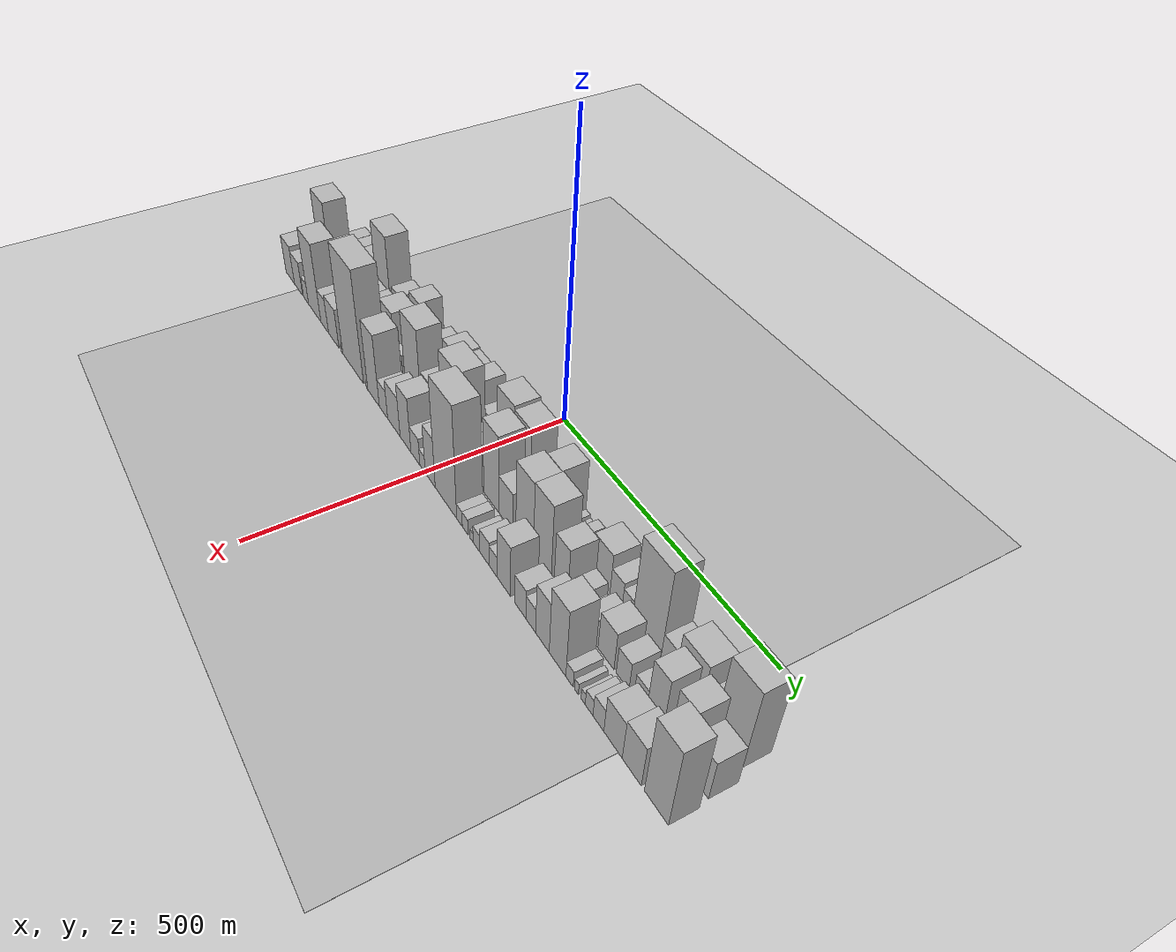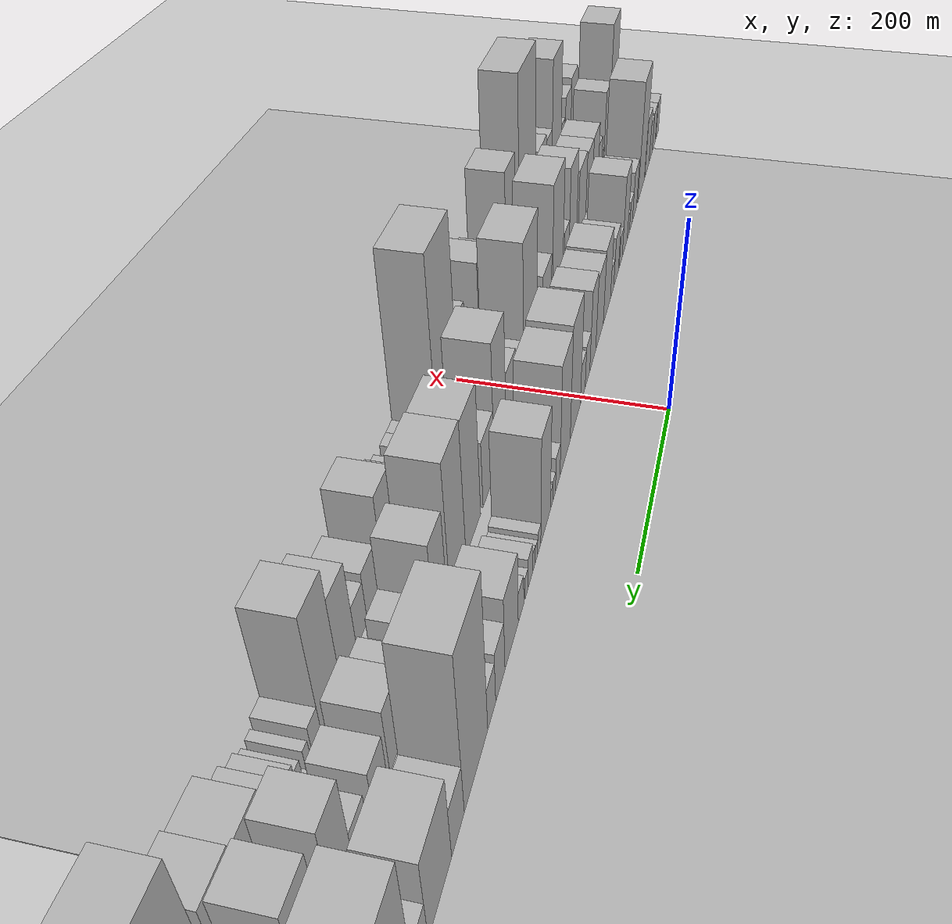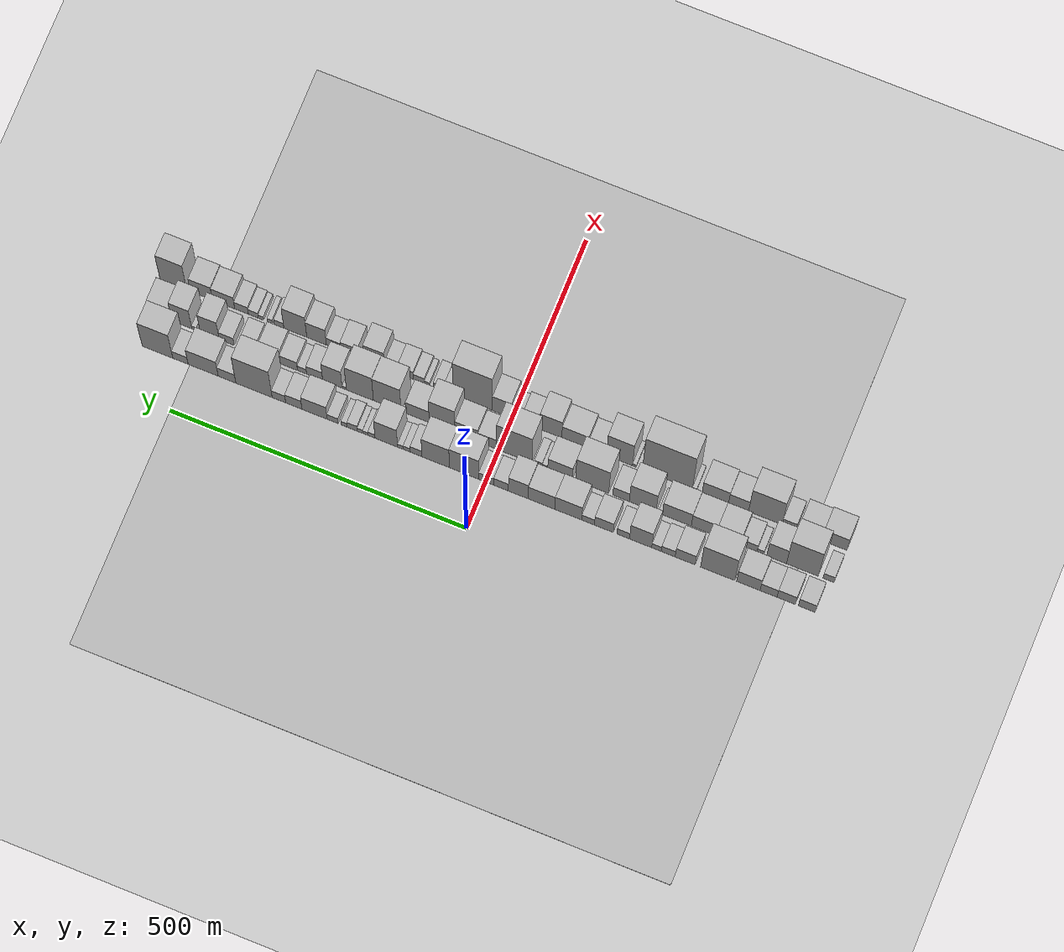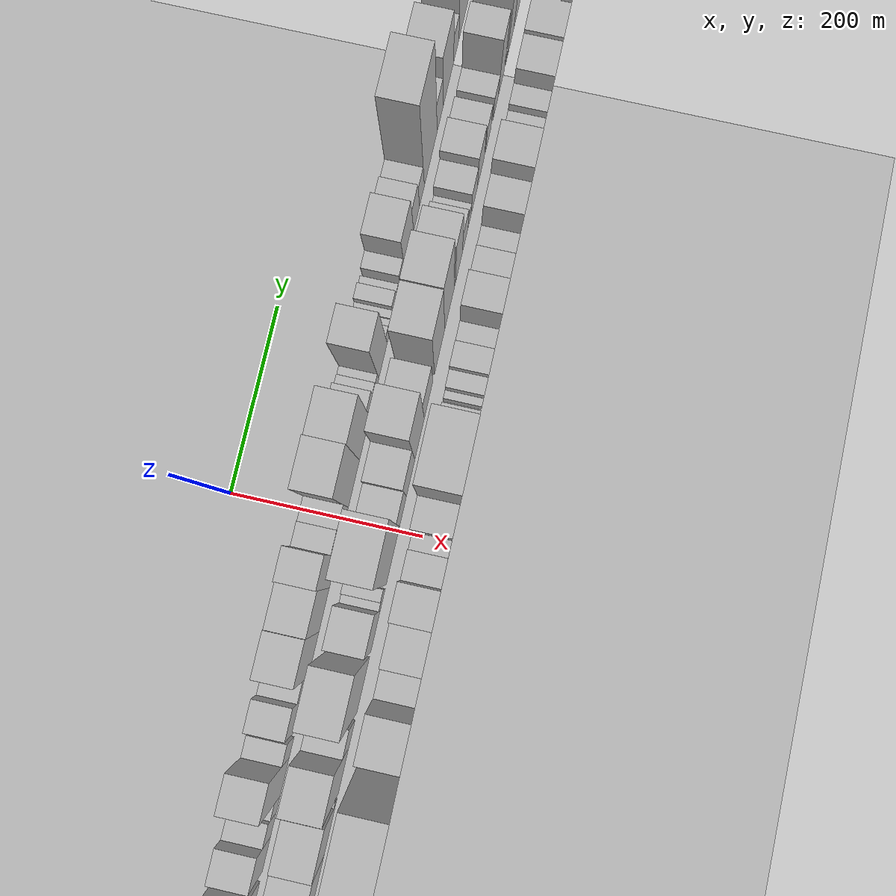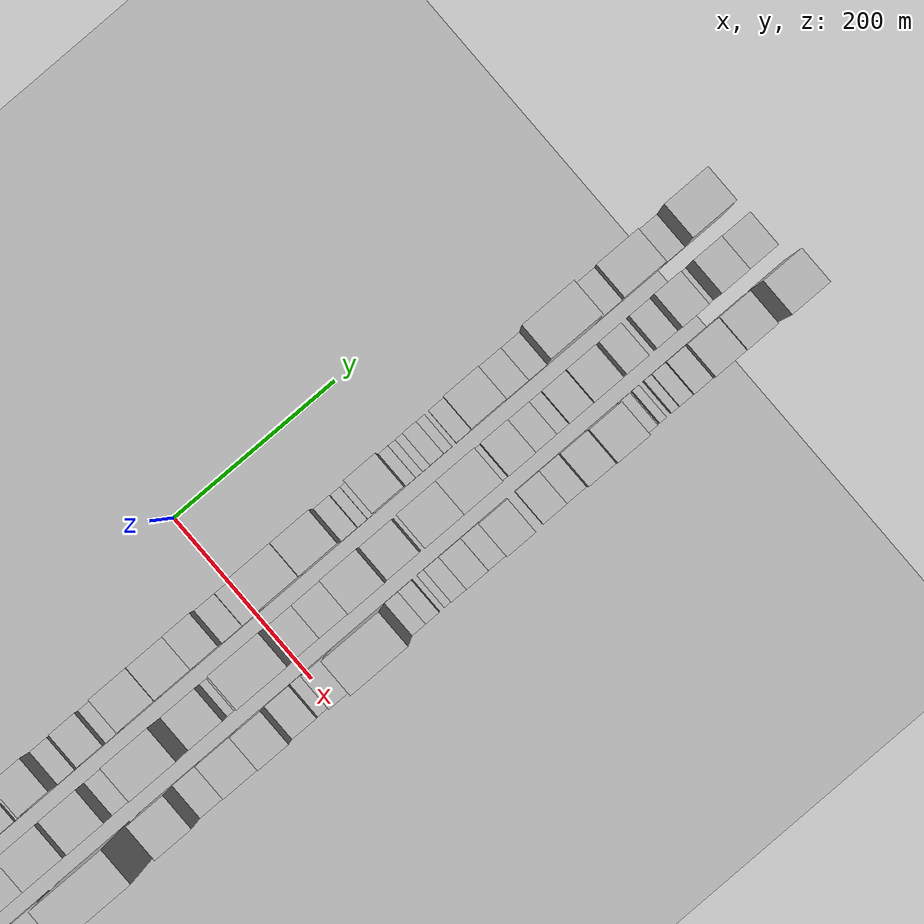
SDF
<?xml version="1.0" encoding="utf-8"?>

<sdf version="1.6">

   <world name="default">

      <gui fullscreen="0">

         <camera name="user_camera">

            <pose>-15 0 4.57585 0 0 0</pose>

            <view_controller>orbit</view_controller>

         </camera>

      </gui>

      <scene>

         <sky>

           <clouds>

             <speed>12</speed>

           </clouds>

         </sky>

         <ambient>0.4 0.4 0.4 1</ambient>

         <background>0.7 0.7 0.7 1</background>

         <shadows>1</shadows>

      </scene>

      <gravity>0 0 -9.8066</gravity>

      <magnetic_field>6e-06 2.3e-05 -4.2e-05</magnetic_field>

      <physics default="0" name="default_physics" type="ode">

         <ode>

            <solver>

               <type>quick</type>

               <iters>10</iters>

               <sor>1.0</sor>

               <use_dynamic_moi_rescaling>0</use_dynamic_moi_rescaling>

            </solver>

            <constraints>

               <cfm>0</cfm>

               <erp>0.2</erp>

               <contact_max_correcting_vel>100</contact_max_correcting_vel>

               <contact_surface_layer>0.001</contact_surface_layer>

            </constraints>

         </ode>

         <max_step_size>0.004</max_step_size>

         <real_time_factor>1</real_time_factor>

         <real_time_update_rate>250</real_time_update_rate>

      </physics>

      <light name="sun" type="directional">

         <cast_shadows>1</cast_shadows>

         <pose>0 0 10 0 0 0</pose>

         <diffuse>0.8 0.8 0.8 1</diffuse>

         <specular>0.2 0.2 0.2 1</specular>

         <attenuation>

            <range>1000</range>

            <constant>0.9</constant>

            <linear>0.01</linear>

            <quadratic>0.001</quadratic>

         </attenuation>

         <direction>-0.5 0.1 -0.9</direction>

      </light>

      <include>

         <name>ground_plane_1</name>

         <uri>model://HANNAS_ground_plane</uri>

         <pose>0 0 0  0 0 0</pose>

      </include>

      <include>

         <name>ground_plane_2</name>

         <uri>model://HANNAS_ground_plane</uri>

         <pose>100 0 0  0 0 0</pose>

      </include>

      <model name="building_1">

         <static>1</static>

         <pose frame="">100.0000 -536.0198 0 0.000000 0.000000 0.000000</pose>

         <link name="link">

            <pose frame="">0 0 25.50 0 0 0</pose>

            <collision name="collision">

               <geometry>

                  <box>

                     <size>40.0000 27.9604 51.0000</size>

                  </box>

               </geometry>

               <max_contacts>10</max_contacts>

               <surface>

                  <contact>

                     <ode/>

                  </contact>

                  <bounce/>

                  <friction>

                     <torsional>

                        <ode/>

                     </torsional>

                     <ode/>

                  </friction>

               </surface>

            </collision>

            <visual name="visual">

               <cast_shadows>0</cast_shadows>

               <geometry>

                  <box>

                     <size>40.0000 27.9604 51.0000</size>

                  </box>

               </geometry>

               <material>

                  <script>

                     <uri>model://HANNAS_wall/materials/scripts</uri>

                     <uri>model://HANNAS_wall/materials/textures</uri>

                     <name>vrc/HANNAS_wall</name>

                  </script>

               </material>

            </visual>

            <self_collide>0</self_collide>

            <enable_wind>0</enable_wind>

            <kinematic>0</kinematic>

         </link>

      </model>

      <model name="building_2">

         <static>1</static>

         <pose frame="">100.0000 -501.8610 0 0.000000 0.000000 0.000000</pose>

         <link name="link">

            <pose frame="">0 0 27.00 0 0 0</pose>

            <collision name="collision">

               <geometry>

                  <box>

                     <size>40.0000 30.3572 54.0000</size>

                  </box>

               </geometry>

               <max_contacts>10</max_contacts>

               <surface>

                  <contact>

                     <ode/>

                  </contact>

                  <bounce/>

                  <friction>

                     <torsional>

                        <ode/>

                     </torsional>

                     <ode/>

                  </friction>

               </surface>

            </collision>

            <visual name="visual">

               <cast_shadows>0</cast_shadows>

               <geometry>

                  <box>

                     <size>40.0000 30.3572 54.0000</size>

                  </box>

               </geometry>

               <material>

                  <script>

                     <uri>model://HANNAS_wall/materials/scripts</uri>

                     <uri>model://HANNAS_wall/materials/textures</uri>

                     <name>vrc/HANNAS_wall</name>

                  </script>

               </material>

            </visual>

            <self_collide>0</self_collide>

            <enable_wind>0</enable_wind>

            <kinematic>0</kinematic>

         </link>

      </model>

      <model name="building_3">

         <static>1</static>

         <pose frame="">100.0000 -472.5539 0 0.000000 0.000000 0.000000</pose>

         <link name="link">

            <pose frame="">0 0 25.50 0 0 0</pose>

            <collision name="collision">

               <geometry>

                  <box>

                     <size>40.0000 28.2571 51.0000</size>

                  </box>

               </geometry>

               <max_contacts>10</max_contacts>

               <surface>

                  <contact>

                     <ode/>

                  </contact>

                  <bounce/>

                  <friction>

                     <torsional>

                        <ode/>

                     </torsional>

                     <ode/>

                  </friction>

               </surface>

            </collision>

            <visual name="visual">

               <cast_shadows>0</cast_shadows>

               <geometry>

                  <box>

                     <size>40.0000 28.2571 51.0000</size>

                  </box>

               </geometry>

               <material>

                  <script>

                     <uri>model://HANNAS_wall/materials/scripts</uri>

                     <uri>model://HANNAS_wall/materials/textures</uri>

                     <name>vrc/HANNAS_wall</name>

                  </script>

               </material>

            </visual>

            <self_collide>0</self_collide>

            <enable_wind>0</enable_wind>

            <kinematic>0</kinematic>

         </link>

      </model>

      <model name="building_4">

         <static>1</static>

         <pose frame="">100.0000 -438.8511 0 0.000000 0.000000 0.000000</pose>

         <link name="link">

            <pose frame="">0 0 37.50 0 0 0</pose>

            <collision name="collision">

               <geometry>

                  <box>

                     <size>40.0000 39.1485 75.0000</size>

                  </box>

               </geometry>

               <max_contacts>10</max_contacts>

               <surface>

                  <contact>

                     <ode/>

                  </contact>

                  <bounce/>

                  <friction>

                     <torsional>

                        <ode/>

                     </torsional>

                     <ode/>

                  </friction>

               </surface>

            </collision>

            <visual name="visual">

               <cast_shadows>0</cast_shadows>

               <geometry>

                  <box>

                     <size>40.0000 39.1485 75.0000</size>

                  </box>

               </geometry>

               <material>

                  <script>

                     <uri>model://HANNAS_wall/materials/scripts</uri>

                     <uri>model://HANNAS_wall/materials/textures</uri>

                     <name>vrc/HANNAS_wall</name>

                  </script>

               </material>

            </visual>

            <self_collide>0</self_collide>

            <enable_wind>0</enable_wind>

            <kinematic>0</kinematic>

         </link>

      </model>

      <model name="building_5">

         <static>1</static>

         <pose frame="">100.0000 -387.6877 0 0.000000 0.000000 0.000000</pose>

         <link name="link">

            <pose frame="">0 0 75.00 0 0 0</pose>

            <collision name="collision">

               <geometry>

                  <box>

                     <size>40.0000 57.1784 150.0000</size>

                  </box>

               </geometry>

               <max_contacts>10</max_contacts>

               <surface>

                  <contact>

                     <ode/>

                  </contact>

                  <bounce/>

                  <friction>

                     <torsional>

                        <ode/>

                     </torsional>

                     <ode/>

                  </friction>

               </surface>

            </collision>

            <visual name="visual">

               <cast_shadows>0</cast_shadows>

               <geometry>

                  <box>

                     <size>40.0000 57.1784 150.0000</size>

                  </box>

               </geometry>

               <material>

                  <script>

                     <uri>model://HANNAS_wall/materials/scripts</uri>

                     <uri>model://HANNAS_wall/materials/textures</uri>

                     <name>vrc/HANNAS_wall</name>

                  </script>

               </material>

            </visual>

            <self_collide>0</self_collide>

            <enable_wind>0</enable_wind>

            <kinematic>0</kinematic>

         </link>

      </model>

      <model name="building_6">

         <static>1</static>

         <pose frame="">100.0000 -333.3778 0 0.000000 0.000000 0.000000</pose>

         <link name="link">

            <pose frame="">0 0 31.50 0 0 0</pose>

            <collision name="collision">

               <geometry>

                  <box>

                     <size>40.0000 33.4414 63.0000</size>

                  </box>

               </geometry>

               <max_contacts>10</max_contacts>

               <surface>

                  <contact>

                     <ode/>

                  </contact>

                  <bounce/>

                  <friction>

                     <torsional>

                        <ode/>

                     </torsional>

                     <ode/>

                  </friction>

               </surface>

            </collision>

            <visual name="visual">

               <cast_shadows>0</cast_shadows>

               <geometry>

                  <box>

                     <size>40.0000 33.4414 63.0000</size>

                  </box>

               </geometry>

               <material>

                  <script>

                     <uri>model://HANNAS_wall/materials/scripts</uri>

                     <uri>model://HANNAS_wall/materials/textures</uri>

                     <name>vrc/HANNAS_wall</name>

                  </script>

               </material>

            </visual>

            <self_collide>0</self_collide>

            <enable_wind>0</enable_wind>

            <kinematic>0</kinematic>

         </link>

      </model>

      <model name="building_7">

         <static>1</static>

         <pose frame="">100.0000 -305.0431 0 0.000000 0.000000 0.000000</pose>

         <link name="link">

            <pose frame="">0 0 19.50 0 0 0</pose>

            <collision name="collision">

               <geometry>

                  <box>

                     <size>40.0000 23.2279 39.0000</size>

                  </box>

               </geometry>

               <max_contacts>10</max_contacts>

               <surface>

                  <contact>

                     <ode/>

                  </contact>

                  <bounce/>

                  <friction>

                     <torsional>

                        <ode/>

                     </torsional>

                     <ode/>

                  </friction>

               </surface>

            </collision>

            <visual name="visual">

               <cast_shadows>0</cast_shadows>

               <geometry>

                  <box>

                     <size>40.0000 23.2279 39.0000</size>

                  </box>

               </geometry>

               <material>

                  <script>

                     <uri>model://HANNAS_wall/materials/scripts</uri>

                     <uri>model://HANNAS_wall/materials/textures</uri>

                     <name>vrc/HANNAS_wall</name>

                  </script>

               </material>

            </visual>

            <self_collide>0</self_collide>

            <enable_wind>0</enable_wind>

            <kinematic>0</kinematic>

         </link>

      </model>

      <model name="building_8">

         <static>1</static>

         <pose frame="">100.0000 -285.4440 0 0.000000 0.000000 0.000000</pose>

         <link name="link">

            <pose frame="">0 0 15.00 0 0 0</pose>

            <collision name="collision">

               <geometry>

                  <box>

                     <size>40.0000 15.9703 30.0000</size>

                  </box>

               </geometry>

               <max_contacts>10</max_contacts>

               <surface>

                  <contact>

                     <ode/>

                  </contact>

                  <bounce/>

                  <friction>

                     <torsional>

                        <ode/>

                     </torsional>

                     <ode/>

                  </friction>

               </surface>

            </collision>

            <visual name="visual">

               <cast_shadows>0</cast_shadows>

               <geometry>

                  <box>

                     <size>40.0000 15.9703 30.0000</size>

                  </box>

               </geometry>

               <material>

                  <script>

                     <uri>model://HANNAS_wall/materials/scripts</uri>

                     <uri>model://HANNAS_wall/materials/textures</uri>

                     <name>vrc/HANNAS_wall</name>

                  </script>

               </material>

            </visual>

            <self_collide>0</self_collide>

            <enable_wind>0</enable_wind>

            <kinematic>0</kinematic>

         </link>

      </model>

      <model name="building_9">

         <static>1</static>

         <pose frame="">100.0000 -258.9687 0 0.000000 0.000000 0.000000</pose>

         <link name="link">

            <pose frame="">0 0 49.50 0 0 0</pose>

            <collision name="collision">

               <geometry>

                  <box>

                     <size>40.0000 36.9803 99.0000</size>

                  </box>

               </geometry>

               <max_contacts>10</max_contacts>

               <surface>

                  <contact>

                     <ode/>

                  </contact>

                  <bounce/>

                  <friction>

                     <torsional>

                        <ode/>

                     </torsional>

                     <ode/>

                  </friction>

               </surface>

            </collision>

            <visual name="visual">

               <cast_shadows>0</cast_shadows>

               <geometry>

                  <box>

                     <size>40.0000 36.9803 99.0000</size>

                  </box>

               </geometry>

               <material>

                  <script>

                     <uri>model://HANNAS_wall/materials/scripts</uri>

                     <uri>model://HANNAS_wall/materials/textures</uri>

                     <name>vrc/HANNAS_wall</name>

                  </script>

               </material>

            </visual>

            <self_collide>0</self_collide>

            <enable_wind>0</enable_wind>

            <kinematic>0</kinematic>

         </link>

      </model>

      <model name="building_10">

         <static>1</static>

         <pose frame="">100.0000 -229.9270 0 0.000000 0.000000 0.000000</pose>

         <link name="link">

            <pose frame="">0 0 19.50 0 0 0</pose>

            <collision name="collision">

               <geometry>

                  <box>

                     <size>40.0000 21.1032 39.0000</size>

                  </box>

               </geometry>

               <max_contacts>10</max_contacts>

               <surface>

                  <contact>

                     <ode/>

                  </contact>

                  <bounce/>

                  <friction>

                     <torsional>

                        <ode/>

                     </torsional>

                     <ode/>

                  </friction>

               </surface>

            </collision>

            <visual name="visual">

               <cast_shadows>0</cast_shadows>

               <geometry>

                  <box>

                     <size>40.0000 21.1032 39.0000</size>

                  </box>

               </geometry>

               <material>

                  <script>

                     <uri>model://HANNAS_wall/materials/scripts</uri>

                     <uri>model://HANNAS_wall/materials/textures</uri>

                     <name>vrc/HANNAS_wall</name>

                  </script>

               </material>

            </visual>

            <self_collide>0</self_collide>

            <enable_wind>0</enable_wind>

            <kinematic>0</kinematic>

         </link>

      </model>

      <model name="building_11">

         <static>1</static>

         <pose frame="">100.0000 -197.5633 0 0.000000 0.000000 0.000000</pose>

         <link name="link">

            <pose frame="">0 0 30.00 0 0 0</pose>

            <collision name="collision">

               <geometry>

                  <box>

                     <size>40.0000 31.6240 60.0000</size>

                  </box>

               </geometry>

               <max_contacts>10</max_contacts>

               <surface>

                  <contact>

                     <ode/>

                  </contact>

                  <bounce/>

                  <friction>

                     <torsional>

                        <ode/>

                     </torsional>

                     <ode/>

                  </friction>

               </surface>

            </collision>

            <visual name="visual">

               <cast_shadows>0</cast_shadows>

               <geometry>

                  <box>

                     <size>40.0000 31.6240 60.0000</size>

                  </box>

               </geometry>

               <material>

                  <script>

                     <uri>model://HANNAS_wall/materials/scripts</uri>

                     <uri>model://HANNAS_wall/materials/textures</uri>

                     <name>vrc/HANNAS_wall</name>

                  </script>

               </material>

            </visual>

            <self_collide>0</self_collide>

            <enable_wind>0</enable_wind>

            <kinematic>0</kinematic>

         </link>

      </model>

      <model name="building_12">

         <static>1</static>

         <pose frame="">100.0000 -171.0606 0 0.000000 0.000000 0.000000</pose>

         <link name="link">

            <pose frame="">0 0 18.00 0 0 0</pose>

            <collision name="collision">

               <geometry>

                  <box>

                     <size>40.0000 21.3814 36.0000</size>

                  </box>

               </geometry>

               <max_contacts>10</max_contacts>

               <surface>

                  <contact>

                     <ode/>

                  </contact>

                  <bounce/>

                  <friction>

                     <torsional>

                        <ode/>

                     </torsional>

                     <ode/>

                  </friction>

               </surface>

            </collision>

            <visual name="visual">

               <cast_shadows>0</cast_shadows>

               <geometry>

                  <box>

                     <size>40.0000 21.3814 36.0000</size>

                  </box>

               </geometry>

               <material>

                  <script>

                     <uri>model://HANNAS_wall/materials/scripts</uri>

                     <uri>model://HANNAS_wall/materials/textures</uri>

                     <name>vrc/HANNAS_wall</name>

                  </script>

               </material>

            </visual>

            <self_collide>0</self_collide>

            <enable_wind>0</enable_wind>

            <kinematic>0</kinematic>

         </link>

      </model>

      <model name="building_13">

         <static>1</static>

         <pose frame="">100.0000 -137.8540 0 0.000000 0.000000 0.000000</pose>

         <link name="link">

            <pose frame="">0 0 43.50 0 0 0</pose>

            <collision name="collision">

               <geometry>

                  <box>

                     <size>40.0000 45.0318 87.0000</size>

                  </box>

               </geometry>

               <max_contacts>10</max_contacts>

               <surface>

                  <contact>

                     <ode/>

                  </contact>

                  <bounce/>

                  <friction>

                     <torsional>

                        <ode/>

                     </torsional>

                     <ode/>

                  </friction>

               </surface>

            </collision>

            <visual name="visual">

               <cast_shadows>0</cast_shadows>

               <geometry>

                  <box>

                     <size>40.0000 45.0318 87.0000</size>

                  </box>

               </geometry>

               <material>

                  <script>

                     <uri>model://HANNAS_wall/materials/scripts</uri>

                     <uri>model://HANNAS_wall/materials/textures</uri>

                     <name>vrc/HANNAS_wall</name>

                  </script>

               </material>

            </visual>

            <self_collide>0</self_collide>

            <enable_wind>0</enable_wind>

            <kinematic>0</kinematic>

         </link>

      </model>

      <model name="building_14">

         <static>1</static>

         <pose frame="">100.0000 -93.0057 0 0.000000 0.000000 0.000000</pose>

         <link name="link">

            <pose frame="">0 0 42.00 0 0 0</pose>

            <collision name="collision">

               <geometry>

                  <box>

                     <size>40.0000 44.6648 84.0000</size>

                  </box>

               </geometry>

               <max_contacts>10</max_contacts>

               <surface>

                  <contact>

                     <ode/>

                  </contact>

                  <bounce/>

                  <friction>

                     <torsional>

                        <ode/>

                     </torsional>

                     <ode/>

                  </friction>

               </surface>

            </collision>

            <visual name="visual">

               <cast_shadows>0</cast_shadows>

               <geometry>

                  <box>

                     <size>40.0000 44.6648 84.0000</size>

                  </box>

               </geometry>

               <material>

                  <script>

                     <uri>model://HANNAS_wall/materials/scripts</uri>

                     <uri>model://HANNAS_wall/materials/textures</uri>

                     <name>vrc/HANNAS_wall</name>

                  </script>

               </material>

            </visual>

            <self_collide>0</self_collide>

            <enable_wind>0</enable_wind>

            <kinematic>0</kinematic>

         </link>

      </model>

      <model name="building_15">

         <static>1</static>

         <pose frame="">100.0000 -54.0988 0 0.000000 0.000000 0.000000</pose>

         <link name="link">

            <pose frame="">0 0 46.50 0 0 0</pose>

            <collision name="collision">

               <geometry>

                  <box>

                     <size>40.0000 33.1490 93.0000</size>

                  </box>

               </geometry>

               <max_contacts>10</max_contacts>

               <surface>

                  <contact>

                     <ode/>

                  </contact>

                  <bounce/>

                  <friction>

                     <torsional>

                        <ode/>

                     </torsional>

                     <ode/>

                  </friction>

               </surface>

            </collision>

            <visual name="visual">

               <cast_shadows>0</cast_shadows>

               <geometry>

                  <box>

                     <size>40.0000 33.1490 93.0000</size>

                  </box>

               </geometry>

               <material>

                  <script>

                     <uri>model://HANNAS_wall/materials/scripts</uri>

                     <uri>model://HANNAS_wall/materials/textures</uri>

                     <name>vrc/HANNAS_wall</name>

                  </script>

               </material>

            </visual>

            <self_collide>0</self_collide>

            <enable_wind>0</enable_wind>

            <kinematic>0</kinematic>

         </link>

      </model>

      <model name="building_16">

         <static>1</static>

         <pose frame="">100.0000 -25.1981 0 0.000000 0.000000 0.000000</pose>

         <link name="link">

            <pose frame="">0 0 24.00 0 0 0</pose>

            <collision name="collision">

               <geometry>

                  <box>

                     <size>40.0000 24.6524 48.0000</size>

                  </box>

               </geometry>

               <max_contacts>10</max_contacts>

               <surface>

                  <contact>

                     <ode/>

                  </contact>

                  <bounce/>

                  <friction>

                     <torsional>

                        <ode/>

                     </torsional>

                     <ode/>

                  </friction>

               </surface>

            </collision>

            <visual name="visual">

               <cast_shadows>0</cast_shadows>

               <geometry>

                  <box>

                     <size>40.0000 24.6524 48.0000</size>

                  </box>

               </geometry>

               <material>

                  <script>

                     <uri>model://HANNAS_wall/materials/scripts</uri>

                     <uri>model://HANNAS_wall/materials/textures</uri>

                     <name>vrc/HANNAS_wall</name>

                  </script>

               </material>

            </visual>

            <self_collide>0</self_collide>

            <enable_wind>0</enable_wind>

            <kinematic>0</kinematic>

         </link>

      </model>

      <model name="building_17">

         <static>1</static>

         <pose frame="">100.0000 -0.3013 0 0.000000 0.000000 0.000000</pose>

         <link name="link">

            <pose frame="">0 0 22.50 0 0 0</pose>

            <collision name="collision">

               <geometry>

                  <box>

                     <size>40.0000 25.1413 45.0000</size>

                  </box>

               </geometry>

               <max_contacts>10</max_contacts>

               <surface>

                  <contact>

                     <ode/>

                  </contact>

                  <bounce/>

                  <friction>

                     <torsional>

                        <ode/>

                     </torsional>

                     <ode/>

                  </friction>

               </surface>

            </collision>

            <visual name="visual">

               <cast_shadows>0</cast_shadows>

               <geometry>

                  <box>

                     <size>40.0000 25.1413 45.0000</size>

                  </box>

               </geometry>

               <material>

                  <script>

                     <uri>model://HANNAS_wall/materials/scripts</uri>

                     <uri>model://HANNAS_wall/materials/textures</uri>

                     <name>vrc/HANNAS_wall</name>

                  </script>

               </material>

            </visual>

            <self_collide>0</self_collide>

            <enable_wind>0</enable_wind>

            <kinematic>0</kinematic>

         </link>

      </model>

      <model name="building_18">

         <static>1</static>

         <pose frame="">100.0000 36.9575 0 0.000000 0.000000 0.000000</pose>

         <link name="link">

            <pose frame="">0 0 63.00 0 0 0</pose>

            <collision name="collision">

               <geometry>

                  <box>

                     <size>40.0000 49.3762 126.0000</size>

                  </box>

               </geometry>

               <max_contacts>10</max_contacts>

               <surface>

                  <contact>

                     <ode/>

                  </contact>

                  <bounce/>

                  <friction>

                     <torsional>

                        <ode/>

                     </torsional>

                     <ode/>

                  </friction>

               </surface>

            </collision>

            <visual name="visual">

               <cast_shadows>0</cast_shadows>

               <geometry>

                  <box>

                     <size>40.0000 49.3762 126.0000</size>

                  </box>

               </geometry>

               <material>

                  <script>

                     <uri>model://HANNAS_wall/materials/scripts</uri>

                     <uri>model://HANNAS_wall/materials/textures</uri>

                     <name>vrc/HANNAS_wall</name>

                  </script>

               </material>

            </visual>

            <self_collide>0</self_collide>

            <enable_wind>0</enable_wind>

            <kinematic>0</kinematic>

         </link>

      </model>

      <model name="building_19">

         <static>1</static>

         <pose frame="">100.0000 84.7058 0 0.000000 0.000000 0.000000</pose>

         <link name="link">

            <pose frame="">0 0 60.00 0 0 0</pose>

            <collision name="collision">

               <geometry>

                  <box>

                     <size>40.0000 46.1204 120.0000</size>

                  </box>

               </geometry>

               <max_contacts>10</max_contacts>

               <surface>

                  <contact>

                     <ode/>

                  </contact>

                  <bounce/>

                  <friction>

                     <torsional>

                        <ode/>

                     </torsional>

                     <ode/>

                  </friction>

               </surface>

            </collision>

            <visual name="visual">

               <cast_shadows>0</cast_shadows>

               <geometry>

                  <box>

                     <size>40.0000 46.1204 120.0000</size>

                  </box>

               </geometry>

               <material>

                  <script>

                     <uri>model://HANNAS_wall/materials/scripts</uri>

                     <uri>model://HANNAS_wall/materials/textures</uri>

                     <name>vrc/HANNAS_wall</name>

                  </script>

               </material>

            </visual>

            <self_collide>0</self_collide>

            <enable_wind>0</enable_wind>

            <kinematic>0</kinematic>

         </link>

      </model>

      <model name="building_20">

         <static>1</static>

         <pose frame="">100.0000 117.5648 0 0.000000 0.000000 0.000000</pose>

         <link name="link">

            <pose frame="">0 0 19.50 0 0 0</pose>

            <collision name="collision">

               <geometry>

                  <box>

                     <size>40.0000 19.5976 39.0000</size>

                  </box>

               </geometry>

               <max_contacts>10</max_contacts>

               <surface>

                  <contact>

                     <ode/>

                  </contact>

                  <bounce/>

                  <friction>

                     <torsional>

                        <ode/>

                     </torsional>

                     <ode/>

                  </friction>

               </surface>

            </collision>

            <visual name="visual">

               <cast_shadows>0</cast_shadows>

               <geometry>

                  <box>

                     <size>40.0000 19.5976 39.0000</size>

                  </box>

               </geometry>

               <material>

                  <script>

                     <uri>model://HANNAS_wall/materials/scripts</uri>

                     <uri>model://HANNAS_wall/materials/textures</uri>

                     <name>vrc/HANNAS_wall</name>

                  </script>

               </material>

            </visual>

            <self_collide>0</self_collide>

            <enable_wind>0</enable_wind>

            <kinematic>0</kinematic>

         </link>

      </model>

      <model name="building_21">

         <static>1</static>

         <pose frame="">100.0000 133.3161 0 0.000000 0.000000 0.000000</pose>

         <link name="link">

            <pose frame="">0 0 12.00 0 0 0</pose>

            <collision name="collision">

               <geometry>

                  <box>

                     <size>40.0000 11.9050 24.0000</size>

                  </box>

               </geometry>

               <max_contacts>10</max_contacts>

               <surface>

                  <contact>

                     <ode/>

                  </contact>

                  <bounce/>

                  <friction>

                     <torsional>

                        <ode/>

                     </torsional>

                     <ode/>

                  </friction>

               </surface>

            </collision>

            <visual name="visual">

               <cast_shadows>0</cast_shadows>

               <geometry>

                  <box>

                     <size>40.0000 11.9050 24.0000</size>

                  </box>

               </geometry>

               <material>

                  <script>

                     <uri>model://HANNAS_wall/materials/scripts</uri>

                     <uri>model://HANNAS_wall/materials/textures</uri>

                     <name>vrc/HANNAS_wall</name>

                  </script>

               </material>

            </visual>

            <self_collide>0</self_collide>

            <enable_wind>0</enable_wind>

            <kinematic>0</kinematic>

         </link>

      </model>

      <model name="building_22">

         <static>1</static>

         <pose frame="">100.0000 144.0258 0 0.000000 0.000000 0.000000</pose>

         <link name="link">

            <pose frame="">0 0 10.50 0 0 0</pose>

            <collision name="collision">

               <geometry>

                  <box>

                     <size>40.0000 9.5144 21.0000</size>

                  </box>

               </geometry>

               <max_contacts>10</max_contacts>

               <surface>

                  <contact>

                     <ode/>

                  </contact>

                  <bounce/>

                  <friction>

                     <torsional>

                        <ode/>

                     </torsional>

                     <ode/>

                  </friction>

               </surface>

            </collision>

            <visual name="visual">

               <cast_shadows>0</cast_shadows>

               <geometry>

                  <box>

                     <size>40.0000 9.5144 21.0000</size>

                  </box>

               </geometry>

               <material>

                  <script>

                     <uri>model://HANNAS_wall/materials/scripts</uri>

                     <uri>model://HANNAS_wall/materials/textures</uri>

                     <name>vrc/HANNAS_wall</name>

                  </script>

               </material>

            </visual>

            <self_collide>0</self_collide>

            <enable_wind>0</enable_wind>

            <kinematic>0</kinematic>

         </link>

      </model>

      <model name="building_23">

         <static>1</static>

         <pose frame="">100.0000 167.7556 0 0.000000 0.000000 0.000000</pose>

         <link name="link">

            <pose frame="">0 0 57.00 0 0 0</pose>

            <collision name="collision">

               <geometry>

                  <box>

                     <size>40.0000 37.9452 114.0000</size>

                  </box>

               </geometry>

               <max_contacts>10</max_contacts>

               <surface>

                  <contact>

                     <ode/>

                  </contact>

                  <bounce/>

                  <friction>

                     <torsional>

                        <ode/>

                     </torsional>

                     <ode/>

                  </friction>

               </surface>

            </collision>

            <visual name="visual">

               <cast_shadows>0</cast_shadows>

               <geometry>

                  <box>

                     <size>40.0000 37.9452 114.0000</size>

                  </box>

               </geometry>

               <material>

                  <script>

                     <uri>model://HANNAS_wall/materials/scripts</uri>

                     <uri>model://HANNAS_wall/materials/textures</uri>

                     <name>vrc/HANNAS_wall</name>

                  </script>

               </material>

            </visual>

            <self_collide>0</self_collide>

            <enable_wind>0</enable_wind>

            <kinematic>0</kinematic>

         </link>

      </model>

      <model name="building_24">

         <static>1</static>

         <pose frame="">100.0000 192.7151 0 0.000000 0.000000 0.000000</pose>

         <link name="link">

            <pose frame="">0 0 12.00 0 0 0</pose>

            <collision name="collision">

               <geometry>

                  <box>

                     <size>40.0000 11.9739 24.0000</size>

                  </box>

               </geometry>

               <max_contacts>10</max_contacts>

               <surface>

                  <contact>

                     <ode/>

                  </contact>

                  <bounce/>

                  <friction>

                     <torsional>

                        <ode/>

                     </torsional>

                     <ode/>

                  </friction>

               </surface>

            </collision>

            <visual name="visual">

               <cast_shadows>0</cast_shadows>

               <geometry>

                  <box>

                     <size>40.0000 11.9739 24.0000</size>

                  </box>

               </geometry>

               <material>

                  <script>

                     <uri>model://HANNAS_wall/materials/scripts</uri>

                     <uri>model://HANNAS_wall/materials/textures</uri>

                     <name>vrc/HANNAS_wall</name>

                  </script>

               </material>

            </visual>

            <self_collide>0</self_collide>

            <enable_wind>0</enable_wind>

            <kinematic>0</kinematic>

         </link>

      </model>

      <model name="building_25">

         <static>1</static>

         <pose frame="">100.0000 203.0524 0 0.000000 0.000000 0.000000</pose>

         <link name="link">

            <pose frame="">0 0 9.00 0 0 0</pose>

            <collision name="collision">

               <geometry>

                  <box>

                     <size>40.0000 8.7008 18.0000</size>

                  </box>

               </geometry>

               <max_contacts>10</max_contacts>

               <surface>

                  <contact>

                     <ode/>

                  </contact>

                  <bounce/>

                  <friction>

                     <torsional>

                        <ode/>

                     </torsional>

                     <ode/>

                  </friction>

               </surface>

            </collision>

            <visual name="visual">

               <cast_shadows>0</cast_shadows>

               <geometry>

                  <box>

                     <size>40.0000 8.7008 18.0000</size>

                  </box>

               </geometry>

               <material>

                  <script>

                     <uri>model://HANNAS_wall/materials/scripts</uri>

                     <uri>model://HANNAS_wall/materials/textures</uri>

                     <name>vrc/HANNAS_wall</name>

                  </script>

               </material>

            </visual>

            <self_collide>0</self_collide>

            <enable_wind>0</enable_wind>

            <kinematic>0</kinematic>

         </link>

      </model>

      <model name="building_26">

         <static>1</static>

         <pose frame="">100.0000 212.0051 0 0.000000 0.000000 0.000000</pose>

         <link name="link">

            <pose frame="">0 0 10.50 0 0 0</pose>

            <collision name="collision">

               <geometry>

                  <box>

                     <size>40.0000 9.2047 21.0000</size>

                  </box>

               </geometry>

               <max_contacts>10</max_contacts>

               <surface>

                  <contact>

                     <ode/>

                  </contact>

                  <bounce/>

                  <friction>

                     <torsional>

                        <ode/>

                     </torsional>

                     <ode/>

                  </friction>

               </surface>

            </collision>

            <visual name="visual">

               <cast_shadows>0</cast_shadows>

               <geometry>

                  <box>

                     <size>40.0000 9.2047 21.0000</size>

                  </box>

               </geometry>

               <material>

                  <script>

                     <uri>model://HANNAS_wall/materials/scripts</uri>

                     <uri>model://HANNAS_wall/materials/textures</uri>

                     <name>vrc/HANNAS_wall</name>

                  </script>

               </material>

            </visual>

            <self_collide>0</self_collide>

            <enable_wind>0</enable_wind>

            <kinematic>0</kinematic>

         </link>

      </model>

      <model name="building_27">

         <static>1</static>

         <pose frame="">100.0000 225.0518 0 0.000000 0.000000 0.000000</pose>

         <link name="link">

            <pose frame="">0 0 16.50 0 0 0</pose>

            <collision name="collision">

               <geometry>

                  <box>

                     <size>40.0000 16.8886 33.0000</size>

                  </box>

               </geometry>

               <max_contacts>10</max_contacts>

               <surface>

                  <contact>

                     <ode/>

                  </contact>

                  <bounce/>

                  <friction>

                     <torsional>

                        <ode/>

                     </torsional>

                     <ode/>

                  </friction>

               </surface>

            </collision>

            <visual name="visual">

               <cast_shadows>0</cast_shadows>

               <geometry>

                  <box>

                     <size>40.0000 16.8886 33.0000</size>

                  </box>

               </geometry>

               <material>

                  <script>

                     <uri>model://HANNAS_wall/materials/scripts</uri>

                     <uri>model://HANNAS_wall/materials/textures</uri>

                     <name>vrc/HANNAS_wall</name>

                  </script>

               </material>

            </visual>

            <self_collide>0</self_collide>

            <enable_wind>0</enable_wind>

            <kinematic>0</kinematic>

         </link>

      </model>

      <model name="building_28">

         <static>1</static>

         <pose frame="">100.0000 238.6537 0 0.000000 0.000000 0.000000</pose>

         <link name="link">

            <pose frame="">0 0 12.00 0 0 0</pose>

            <collision name="collision">

               <geometry>

                  <box>

                     <size>40.0000 10.3152 24.0000</size>

                  </box>

               </geometry>

               <max_contacts>10</max_contacts>

               <surface>

                  <contact>

                     <ode/>

                  </contact>

                  <bounce/>

                  <friction>

                     <torsional>

                        <ode/>

                     </torsional>

                     <ode/>

                  </friction>

               </surface>

            </collision>

            <visual name="visual">

               <cast_shadows>0</cast_shadows>

               <geometry>

                  <box>

                     <size>40.0000 10.3152 24.0000</size>

                  </box>

               </geometry>

               <material>

                  <script>

                     <uri>model://HANNAS_wall/materials/scripts</uri>

                     <uri>model://HANNAS_wall/materials/textures</uri>

                     <name>vrc/HANNAS_wall</name>

                  </script>

               </material>

            </visual>

            <self_collide>0</self_collide>

            <enable_wind>0</enable_wind>

            <kinematic>0</kinematic>

         </link>

      </model>

      <model name="building_29">

         <static>1</static>

         <pose frame="">100.0000 258.1720 0 0.000000 0.000000 0.000000</pose>

         <link name="link">

            <pose frame="">0 0 16.50 0 0 0</pose>

            <collision name="collision">

               <geometry>

                  <box>

                     <size>40.0000 18.7214 33.0000</size>

                  </box>

               </geometry>

               <max_contacts>10</max_contacts>

               <surface>

                  <contact>

                     <ode/>

                  </contact>

                  <bounce/>

                  <friction>

                     <torsional>

                        <ode/>

                     </torsional>

                     <ode/>

                  </friction>

               </surface>

            </collision>

            <visual name="visual">

               <cast_shadows>0</cast_shadows>

               <geometry>

                  <box>

                     <size>40.0000 18.7214 33.0000</size>

                  </box>

               </geometry>

               <material>

                  <script>

                     <uri>model://HANNAS_wall/materials/scripts</uri>

                     <uri>model://HANNAS_wall/materials/textures</uri>

                     <name>vrc/HANNAS_wall</name>

                  </script>

               </material>

            </visual>

            <self_collide>0</self_collide>

            <enable_wind>0</enable_wind>

            <kinematic>0</kinematic>

         </link>

      </model>

      <model name="building_30">

         <static>1</static>

         <pose frame="">100.0000 288.7846 0 0.000000 0.000000 0.000000</pose>

         <link name="link">

            <pose frame="">0 0 39.00 0 0 0</pose>

            <collision name="collision">

               <geometry>

                  <box>

                     <size>40.0000 42.5040 78.0000</size>

                  </box>

               </geometry>

               <max_contacts>10</max_contacts>

               <surface>

                  <contact>

                     <ode/>

                  </contact>

                  <bounce/>

                  <friction>

                     <torsional>

                        <ode/>

                     </torsional>

                     <ode/>

                  </friction>

               </surface>

            </collision>

            <visual name="visual">

               <cast_shadows>0</cast_shadows>

               <geometry>

                  <box>

                     <size>40.0000 42.5040 78.0000</size>

                  </box>

               </geometry>

               <material>

                  <script>

                     <uri>model://HANNAS_wall/materials/scripts</uri>

                     <uri>model://HANNAS_wall/materials/textures</uri>

                     <name>vrc/HANNAS_wall</name>

                  </script>

               </material>

            </visual>

            <self_collide>0</self_collide>

            <enable_wind>0</enable_wind>

            <kinematic>0</kinematic>

         </link>

      </model>

      <model name="building_31">

         <static>1</static>

         <pose frame="">100.0000 323.8512 0 0.000000 0.000000 0.000000</pose>

         <link name="link">

            <pose frame="">0 0 27.00 0 0 0</pose>

            <collision name="collision">

               <geometry>

                  <box>

                     <size>40.0000 27.6292 54.0000</size>

                  </box>

               </geometry>

               <max_contacts>10</max_contacts>

               <surface>

                  <contact>

                     <ode/>

                  </contact>

                  <bounce/>

                  <friction>

                     <torsional>

                        <ode/>

                     </torsional>

                     <ode/>

                  </friction>

               </surface>

            </collision>

            <visual name="visual">

               <cast_shadows>0</cast_shadows>

               <geometry>

                  <box>

                     <size>40.0000 27.6292 54.0000</size>

                  </box>

               </geometry>

               <material>

                  <script>

                     <uri>model://HANNAS_wall/materials/scripts</uri>

                     <uri>model://HANNAS_wall/materials/textures</uri>

                     <name>vrc/HANNAS_wall</name>

                  </script>

               </material>

            </visual>

            <self_collide>0</self_collide>

            <enable_wind>0</enable_wind>

            <kinematic>0</kinematic>

         </link>

      </model>

      <model name="building_32">

         <static>1</static>

         <pose frame="">100.0000 349.0639 0 0.000000 0.000000 0.000000</pose>

         <link name="link">

            <pose frame="">0 0 22.50 0 0 0</pose>

            <collision name="collision">

               <geometry>

                  <box>

                     <size>40.0000 22.7960 45.0000</size>

                  </box>

               </geometry>

               <max_contacts>10</max_contacts>

               <surface>

                  <contact>

                     <ode/>

                  </contact>

                  <bounce/>

                  <friction>

                     <torsional>

                        <ode/>

                     </torsional>

                     <ode/>

                  </friction>

               </surface>

            </collision>

            <visual name="visual">

               <cast_shadows>0</cast_shadows>

               <geometry>

                  <box>

                     <size>40.0000 22.7960 45.0000</size>

                  </box>

               </geometry>

               <material>

                  <script>

                     <uri>model://HANNAS_wall/materials/scripts</uri>

                     <uri>model://HANNAS_wall/materials/textures</uri>

                     <name>vrc/HANNAS_wall</name>

                  </script>

               </material>

            </visual>

            <self_collide>0</self_collide>

            <enable_wind>0</enable_wind>

            <kinematic>0</kinematic>

         </link>

      </model>

      <model name="building_33">

         <static>1</static>

         <pose frame="">100.0000 391.1682 0 0.000000 0.000000 0.000000</pose>

         <link name="link">

            <pose frame="">0 0 82.50 0 0 0</pose>

            <collision name="collision">

               <geometry>

                  <box>

                     <size>40.0000 61.4127 165.0000</size>

                  </box>

               </geometry>

               <max_contacts>10</max_contacts>

               <surface>

                  <contact>

                     <ode/>

                  </contact>

                  <bounce/>

                  <friction>

                     <torsional>

                        <ode/>

                     </torsional>

                     <ode/>

                  </friction>

               </surface>

            </collision>

            <visual name="visual">

               <cast_shadows>0</cast_shadows>

               <geometry>

                  <box>

                     <size>40.0000 61.4127 165.0000</size>

                  </box>

               </geometry>

               <material>

                  <script>

                     <uri>model://HANNAS_wall/materials/scripts</uri>

                     <uri>model://HANNAS_wall/materials/textures</uri>

                     <name>vrc/HANNAS_wall</name>

                  </script>

               </material>

            </visual>

            <self_collide>0</self_collide>

            <enable_wind>0</enable_wind>

            <kinematic>0</kinematic>

         </link>

      </model>

      <model name="building_34">

         <static>1</static>

         <pose frame="">100.0000 436.8988 0 0.000000 0.000000 0.000000</pose>

         <link name="link">

            <pose frame="">0 0 27.00 0 0 0</pose>

            <collision name="collision">

               <geometry>

                  <box>

                     <size>40.0000 30.0485 54.0000</size>

                  </box>

               </geometry>

               <max_contacts>10</max_contacts>

               <surface>

                  <contact>

                     <ode/>

                  </contact>

                  <bounce/>

                  <friction>

                     <torsional>

                        <ode/>

                     </torsional>

                     <ode/>

                  </friction>

               </surface>

            </collision>

            <visual name="visual">

               <cast_shadows>0</cast_shadows>

               <geometry>

                  <box>

                     <size>40.0000 30.0485 54.0000</size>

                  </box>

               </geometry>

               <material>

                  <script>

                     <uri>model://HANNAS_wall/materials/scripts</uri>

                     <uri>model://HANNAS_wall/materials/textures</uri>

                     <name>vrc/HANNAS_wall</name>

                  </script>

               </material>

            </visual>

            <self_collide>0</self_collide>

            <enable_wind>0</enable_wind>

            <kinematic>0</kinematic>

         </link>

      </model>

      <model name="building_35">

         <static>1</static>

         <pose frame="">100.0000 477.3324 0 0.000000 0.000000 0.000000</pose>

         <link name="link">

            <pose frame="">0 0 45.00 0 0 0</pose>

            <collision name="collision">

               <geometry>

                  <box>

                     <size>40.0000 50.8187 90.0000</size>

                  </box>

               </geometry>

               <max_contacts>10</max_contacts>

               <surface>

                  <contact>

                     <ode/>

                  </contact>

                  <bounce/>

                  <friction>

                     <torsional>

                        <ode/>

                     </torsional>

                     <ode/>

                  </friction>

               </surface>

            </collision>

            <visual name="visual">

               <cast_shadows>0</cast_shadows>

               <geometry>

                  <box>

                     <size>40.0000 50.8187 90.0000</size>

                  </box>

               </geometry>

               <material>

                  <script>

                     <uri>model://HANNAS_wall/materials/scripts</uri>

                     <uri>model://HANNAS_wall/materials/textures</uri>

                     <name>vrc/HANNAS_wall</name>

                  </script>

               </material>

            </visual>

            <self_collide>0</self_collide>

            <enable_wind>0</enable_wind>

            <kinematic>0</kinematic>

         </link>

      </model>

      <model name="building_36">

         <static>1</static>

         <pose frame="">100.0000 515.8046 0 0.000000 0.000000 0.000000</pose>

         <link name="link">

            <pose frame="">0 0 22.50 0 0 0</pose>

            <collision name="collision">

               <geometry>

                  <box>

                     <size>40.0000 26.1258 45.0000</size>

                  </box>

               </geometry>

               <max_contacts>10</max_contacts>

               <surface>

                  <contact>

                     <ode/>

                  </contact>

                  <bounce/>

                  <friction>

                     <torsional>

                        <ode/>

                     </torsional>

                     <ode/>

                  </friction>

               </surface>

            </collision>

            <visual name="visual">

               <cast_shadows>0</cast_shadows>

               <geometry>

                  <box>

                     <size>40.0000 26.1258 45.0000</size>

                  </box>

               </geometry>

               <material>

                  <script>

                     <uri>model://HANNAS_wall/materials/scripts</uri>

                     <uri>model://HANNAS_wall/materials/textures</uri>

                     <name>vrc/HANNAS_wall</name>

                  </script>

               </material>

            </visual>

            <self_collide>0</self_collide>

            <enable_wind>0</enable_wind>

            <kinematic>0</kinematic>

         </link>

      </model>

      <model name="building_37">

         <static>1</static>

         <pose frame="">100.0000 554.7677 0 0.000000 0.000000 0.000000</pose>

         <link name="link">

            <pose frame="">0 0 72.00 0 0 0</pose>

            <collision name="collision">

               <geometry>

                  <box>

                     <size>40.0000 51.8003 144.0000</size>

                  </box>

               </geometry>

               <max_contacts>10</max_contacts>

               <surface>

                  <contact>

                     <ode/>

                  </contact>

                  <bounce/>

                  <friction>

                     <torsional>

                        <ode/>

                     </torsional>

                     <ode/>

                  </friction>

               </surface>

            </collision>

            <visual name="visual">

               <cast_shadows>0</cast_shadows>

               <geometry>

                  <box>

                     <size>40.0000 51.8003 144.0000</size>

                  </box>

               </geometry>

               <material>

                  <script>

                     <uri>model://HANNAS_wall/materials/scripts</uri>

                     <uri>model://HANNAS_wall/materials/textures</uri>

                     <name>vrc/HANNAS_wall</name>

                  </script>

               </material>

            </visual>

            <self_collide>0</self_collide>

            <enable_wind>0</enable_wind>

            <kinematic>0</kinematic>

         </link>

      </model>

      <model name="building_38">

         <static>1</static>

         <pose frame="">155.0000 -550.7602 0 0.000000 0.000000 0.000000</pose>

         <link name="link">

            <pose frame="">0 0 18.00 0 0 0</pose>

            <collision name="collision">

               <geometry>

                  <box>

                     <size>40.0000 18.4797 36.0000</size>

                  </box>

               </geometry>

               <max_contacts>10</max_contacts>

               <surface>

                  <contact>

                     <ode/>

                  </contact>

                  <bounce/>

                  <friction>

                     <torsional>

                        <ode/>

                     </torsional>

                     <ode/>

                  </friction>

               </surface>

            </collision>

            <visual name="visual">

               <cast_shadows>0</cast_shadows>

               <geometry>

                  <box>

                     <size>40.0000 18.4797 36.0000</size>

                  </box>

               </geometry>

               <material>

                  <script>

                     <uri>model://HANNAS_wall/materials/scripts</uri>

                     <uri>model://HANNAS_wall/materials/textures</uri>

                     <name>vrc/HANNAS_wall</name>

                  </script>

               </material>

            </visual>

            <self_collide>0</self_collide>

            <enable_wind>0</enable_wind>

            <kinematic>0</kinematic>

         </link>

      </model>

      <model name="building_39">

         <static>1</static>

         <pose frame="">155.0000 -507.0626 0 0.000000 0.000000 0.000000</pose>

         <link name="link">

            <pose frame="">0 0 81.00 0 0 0</pose>

            <collision name="collision">

               <geometry>

                  <box>

                     <size>40.0000 52.9155 162.0000</size>

                  </box>

               </geometry>

               <max_contacts>10</max_contacts>

               <surface>

                  <contact>

                     <ode/>

                  </contact>

                  <bounce/>

                  <friction>

                     <torsional>

                        <ode/>

                     </torsional>

                     <ode/>

                  </friction>

               </surface>

            </collision>

            <visual name="visual">

               <cast_shadows>0</cast_shadows>

               <geometry>

                  <box>

                     <size>40.0000 52.9155 162.0000</size>

                  </box>

               </geometry>

               <material>

                  <script>

                     <uri>model://HANNAS_wall/materials/scripts</uri>

                     <uri>model://HANNAS_wall/materials/textures</uri>

                     <name>vrc/HANNAS_wall</name>

                  </script>

               </material>

            </visual>

            <self_collide>0</self_collide>

            <enable_wind>0</enable_wind>

            <kinematic>0</kinematic>

         </link>

      </model>

      <model name="building_40">

         <static>1</static>

         <pose frame="">155.0000 -464.2342 0 0.000000 0.000000 0.000000</pose>

         <link name="link">

            <pose frame="">0 0 46.50 0 0 0</pose>

            <collision name="collision">

               <geometry>

                  <box>

                     <size>40.0000 32.7412 93.0000</size>

                  </box>

               </geometry>

               <max_contacts>10</max_contacts>

               <surface>

                  <contact>

                     <ode/>

                  </contact>

                  <bounce/>

                  <friction>

                     <torsional>

                        <ode/>

                     </torsional>

                     <ode/>

                  </friction>

               </surface>

            </collision>

            <visual name="visual">

               <cast_shadows>0</cast_shadows>

               <geometry>

                  <box>

                     <size>40.0000 32.7412 93.0000</size>

                  </box>

               </geometry>

               <material>

                  <script>

                     <uri>model://HANNAS_wall/materials/scripts</uri>

                     <uri>model://HANNAS_wall/materials/textures</uri>

                     <name>vrc/HANNAS_wall</name>

                  </script>

               </material>

            </visual>

            <self_collide>0</self_collide>

            <enable_wind>0</enable_wind>

            <kinematic>0</kinematic>

         </link>

      </model>

      <model name="building_41">

         <static>1</static>

         <pose frame="">155.0000 -437.2215 0 0.000000 0.000000 0.000000</pose>

         <link name="link">

            <pose frame="">0 0 12.00 0 0 0</pose>

            <collision name="collision">

               <geometry>

                  <box>

                     <size>40.0000 11.2841 24.0000</size>

                  </box>

               </geometry>

               <max_contacts>10</max_contacts>

               <surface>

                  <contact>

                     <ode/>

                  </contact>

                  <bounce/>

                  <friction>

                     <torsional>

                        <ode/>

                     </torsional>

                     <ode/>

                  </friction>

               </surface>

            </collision>

            <visual name="visual">

               <cast_shadows>0</cast_shadows>

               <geometry>

                  <box>

                     <size>40.0000 11.2841 24.0000</size>

                  </box>

               </geometry>

               <material>

                  <script>

                     <uri>model://HANNAS_wall/materials/scripts</uri>

                     <uri>model://HANNAS_wall/materials/textures</uri>

                     <name>vrc/HANNAS_wall</name>

                  </script>

               </material>

            </visual>

            <self_collide>0</self_collide>

            <enable_wind>0</enable_wind>

            <kinematic>0</kinematic>

         </link>

      </model>

      <model name="building_42">

         <static>1</static>

         <pose frame="">155.0000 -418.3878 0 0.000000 0.000000 0.000000</pose>

         <link name="link">

            <pose frame="">0 0 22.50 0 0 0</pose>

            <collision name="collision">

               <geometry>

                  <box>

                     <size>40.0000 26.3834 45.0000</size>

                  </box>

               </geometry>

               <max_contacts>10</max_contacts>

               <surface>

                  <contact>

                     <ode/>

                  </contact>

                  <bounce/>

                  <friction>

                     <torsional>

                        <ode/>

                     </torsional>

                     <ode/>

                  </friction>

               </surface>

            </collision>

            <visual name="visual">

               <cast_shadows>0</cast_shadows>

               <geometry>

                  <box>

                     <size>40.0000 26.3834 45.0000</size>

                  </box>

               </geometry>

               <material>

                  <script>

                     <uri>model://HANNAS_wall/materials/scripts</uri>

                     <uri>model://HANNAS_wall/materials/textures</uri>

                     <name>vrc/HANNAS_wall</name>

                  </script>

               </material>

            </visual>

            <self_collide>0</self_collide>

            <enable_wind>0</enable_wind>

            <kinematic>0</kinematic>

         </link>

      </model>

      <model name="building_43">

         <static>1</static>

         <pose frame="">155.0000 -384.8480 0 0.000000 0.000000 0.000000</pose>

         <link name="link">

            <pose frame="">0 0 37.50 0 0 0</pose>

            <collision name="collision">

               <geometry>

                  <box>

                     <size>40.0000 40.6961 75.0000</size>

                  </box>

               </geometry>

               <max_contacts>10</max_contacts>

               <surface>

                  <contact>

                     <ode/>

                  </contact>

                  <bounce/>

                  <friction>

                     <torsional>

                        <ode/>

                     </torsional>

                     <ode/>

                  </friction>

               </surface>

            </collision>

            <visual name="visual">

               <cast_shadows>0</cast_shadows>

               <geometry>

                  <box>

                     <size>40.0000 40.6961 75.0000</size>

                  </box>

               </geometry>

               <material>

                  <script>

                     <uri>model://HANNAS_wall/materials/scripts</uri>

                     <uri>model://HANNAS_wall/materials/textures</uri>

                     <name>vrc/HANNAS_wall</name>

                  </script>

               </material>

            </visual>

            <self_collide>0</self_collide>

            <enable_wind>0</enable_wind>

            <kinematic>0</kinematic>

         </link>

      </model>

      <model name="building_44">

         <static>1</static>

         <pose frame="">155.0000 -343.2019 0 0.000000 0.000000 0.000000</pose>

         <link name="link">

            <pose frame="">0 0 37.50 0 0 0</pose>

            <collision name="collision">

               <geometry>

                  <box>

                     <size>40.0000 42.5960 75.0000</size>

                  </box>

               </geometry>

               <max_contacts>10</max_contacts>

               <surface>

                  <contact>

                     <ode/>

                  </contact>

                  <bounce/>

                  <friction>

                     <torsional>

                        <ode/>

                     </torsional>

                     <ode/>

                  </friction>

               </surface>

            </collision>

            <visual name="visual">

               <cast_shadows>0</cast_shadows>

               <geometry>

                  <box>

                     <size>40.0000 42.5960 75.0000</size>

                  </box>

               </geometry>

               <material>

                  <script>

                     <uri>model://HANNAS_wall/materials/scripts</uri>

                     <uri>model://HANNAS_wall/materials/textures</uri>

                     <name>vrc/HANNAS_wall</name>

                  </script>

               </material>

            </visual>

            <self_collide>0</self_collide>

            <enable_wind>0</enable_wind>

            <kinematic>0</kinematic>

         </link>

      </model>

      <model name="building_45">

         <static>1</static>

         <pose frame="">155.0000 -297.6463 0 0.000000 0.000000 0.000000</pose>

         <link name="link">

            <pose frame="">0 0 40.50 0 0 0</pose>

            <collision name="collision">

               <geometry>

                  <box>

                     <size>40.0000 48.5152 81.0000</size>

                  </box>

               </geometry>

               <max_contacts>10</max_contacts>

               <surface>

                  <contact>

                     <ode/>

                  </contact>

                  <bounce/>

                  <friction>

                     <torsional>

                        <ode/>

                     </torsional>

                     <ode/>

                  </friction>

               </surface>

            </collision>

            <visual name="visual">

               <cast_shadows>0</cast_shadows>

               <geometry>

                  <box>

                     <size>40.0000 48.5152 81.0000</size>

                  </box>

               </geometry>

               <material>

                  <script>

                     <uri>model://HANNAS_wall/materials/scripts</uri>

                     <uri>model://HANNAS_wall/materials/textures</uri>

                     <name>vrc/HANNAS_wall</name>

                  </script>

               </material>

            </visual>

            <self_collide>0</self_collide>

            <enable_wind>0</enable_wind>

            <kinematic>0</kinematic>

         </link>

      </model>

      <model name="building_46">

         <static>1</static>

         <pose frame="">155.0000 -270.0668 0 0.000000 0.000000 0.000000</pose>

         <link name="link">

            <pose frame="">0 0 7.50 0 0 0</pose>

            <collision name="collision">

               <geometry>

                  <box>

                     <size>40.0000 6.6439 15.0000</size>

                  </box>

               </geometry>

               <max_contacts>10</max_contacts>

               <surface>

                  <contact>

                     <ode/>

                  </contact>

                  <bounce/>

                  <friction>

                     <torsional>

                        <ode/>

                     </torsional>

                     <ode/>

                  </friction>

               </surface>

            </collision>

            <visual name="visual">

               <cast_shadows>0</cast_shadows>

               <geometry>

                  <box>

                     <size>40.0000 6.6439 15.0000</size>

                  </box>

               </geometry>

               <material>

                  <script>

                     <uri>model://HANNAS_wall/materials/scripts</uri>

                     <uri>model://HANNAS_wall/materials/textures</uri>

                     <name>vrc/HANNAS_wall</name>

                  </script>

               </material>

            </visual>

            <self_collide>0</self_collide>

            <enable_wind>0</enable_wind>

            <kinematic>0</kinematic>

         </link>

      </model>

      <model name="building_47">

         <static>1</static>

         <pose frame="">155.0000 -240.4129 0 0.000000 0.000000 0.000000</pose>

         <link name="link">

            <pose frame="">0 0 57.00 0 0 0</pose>

            <collision name="collision">

               <geometry>

                  <box>

                     <size>40.0000 44.6639 114.0000</size>

                  </box>

               </geometry>

               <max_contacts>10</max_contacts>

               <surface>

                  <contact>

                     <ode/>

                  </contact>

                  <bounce/>

                  <friction>

                     <torsional>

                        <ode/>

                     </torsional>

                     <ode/>

                  </friction>

               </surface>

            </collision>

            <visual name="visual">

               <cast_shadows>0</cast_shadows>

               <geometry>

                  <box>

                     <size>40.0000 44.6639 114.0000</size>

                  </box>

               </geometry>

               <material>

                  <script>

                     <uri>model://HANNAS_wall/materials/scripts</uri>

                     <uri>model://HANNAS_wall/materials/textures</uri>

                     <name>vrc/HANNAS_wall</name>

                  </script>

               </material>

            </visual>

            <self_collide>0</self_collide>

            <enable_wind>0</enable_wind>

            <kinematic>0</kinematic>

         </link>

      </model>

      <model name="building_48">

         <static>1</static>

         <pose frame="">155.0000 -204.3218 0 0.000000 0.000000 0.000000</pose>

         <link name="link">

            <pose frame="">0 0 27.00 0 0 0</pose>

            <collision name="collision">

               <geometry>

                  <box>

                     <size>40.0000 27.5182 54.0000</size>

                  </box>

               </geometry>

               <max_contacts>10</max_contacts>

               <surface>

                  <contact>

                     <ode/>

                  </contact>

                  <bounce/>

                  <friction>

                     <torsional>

                        <ode/>

                     </torsional>

                     <ode/>

                  </friction>

               </surface>

            </collision>

            <visual name="visual">

               <cast_shadows>0</cast_shadows>

               <geometry>

                  <box>

                     <size>40.0000 27.5182 54.0000</size>

                  </box>

               </geometry>

               <material>

                  <script>

                     <uri>model://HANNAS_wall/materials/scripts</uri>

                     <uri>model://HANNAS_wall/materials/textures</uri>

                     <name>vrc/HANNAS_wall</name>

                  </script>

               </material>

            </visual>

            <self_collide>0</self_collide>

            <enable_wind>0</enable_wind>

            <kinematic>0</kinematic>

         </link>

      </model>

      <model name="building_49">

         <static>1</static>

         <pose frame="">155.0000 -155.7295 0 0.000000 0.000000 0.000000</pose>

         <link name="link">

            <pose frame="">0 0 72.00 0 0 0</pose>

            <collision name="collision">

               <geometry>

                  <box>

                     <size>40.0000 55.6664 144.0000</size>

                  </box>

               </geometry>

               <max_contacts>10</max_contacts>

               <surface>

                  <contact>

                     <ode/>

                  </contact>

                  <bounce/>

                  <friction>

                     <torsional>

                        <ode/>

                     </torsional>

                     <ode/>

                  </friction>

               </surface>

            </collision>

            <visual name="visual">

               <cast_shadows>0</cast_shadows>

               <geometry>

                  <box>

                     <size>40.0000 55.6664 144.0000</size>

                  </box>

               </geometry>

               <material>

                  <script>

                     <uri>model://HANNAS_wall/materials/scripts</uri>

                     <uri>model://HANNAS_wall/materials/textures</uri>

                     <name>vrc/HANNAS_wall</name>

                  </script>

               </material>

            </visual>

            <self_collide>0</self_collide>

            <enable_wind>0</enable_wind>

            <kinematic>0</kinematic>

         </link>

      </model>

      <model name="building_50">

         <static>1</static>

         <pose frame="">155.0000 -102.1150 0 0.000000 0.000000 0.000000</pose>

         <link name="link">

            <pose frame="">0 0 36.00 0 0 0</pose>

            <collision name="collision">

               <geometry>

                  <box>

                     <size>40.0000 41.5627 72.0000</size>

                  </box>

               </geometry>

               <max_contacts>10</max_contacts>

               <surface>

                  <contact>

                     <ode/>

                  </contact>

                  <bounce/>

                  <friction>

                     <torsional>

                        <ode/>

                     </torsional>

                     <ode/>

                  </friction>

               </surface>

            </collision>

            <visual name="visual">

               <cast_shadows>0</cast_shadows>

               <geometry>

                  <box>

                     <size>40.0000 41.5627 72.0000</size>

                  </box>

               </geometry>

               <material>

                  <script>

                     <uri>model://HANNAS_wall/materials/scripts</uri>

                     <uri>model://HANNAS_wall/materials/textures</uri>

                     <name>vrc/HANNAS_wall</name>

                  </script>

               </material>

            </visual>

            <self_collide>0</self_collide>

            <enable_wind>0</enable_wind>

            <kinematic>0</kinematic>

         </link>

      </model>

      <model name="building_51">

         <static>1</static>

         <pose frame="">155.0000 -76.7715 0 0.000000 0.000000 0.000000</pose>

         <link name="link">

            <pose frame="">0 0 10.50 0 0 0</pose>

            <collision name="collision">

               <geometry>

                  <box>

                     <size>40.0000 9.1243 21.0000</size>

                  </box>

               </geometry>

               <max_contacts>10</max_contacts>

               <surface>

                  <contact>

                     <ode/>

                  </contact>

                  <bounce/>

                  <friction>

                     <torsional>

                        <ode/>

                     </torsional>

                     <ode/>

                  </friction>

               </surface>

            </collision>

            <visual name="visual">

               <cast_shadows>0</cast_shadows>

               <geometry>

                  <box>

                     <size>40.0000 9.1243 21.0000</size>

                  </box>

               </geometry>

               <material>

                  <script>

                     <uri>model://HANNAS_wall/materials/scripts</uri>

                     <uri>model://HANNAS_wall/materials/textures</uri>

                     <name>vrc/HANNAS_wall</name>

                  </script>

               </material>

            </visual>

            <self_collide>0</self_collide>

            <enable_wind>0</enable_wind>

            <kinematic>0</kinematic>

         </link>

      </model>

      <model name="building_52">

         <static>1</static>

         <pose frame="">155.0000 -65.6060 0 0.000000 0.000000 0.000000</pose>

         <link name="link">

            <pose frame="">0 0 13.50 0 0 0</pose>

            <collision name="collision">

               <geometry>

                  <box>

                     <size>40.0000 13.2067 27.0000</size>

                  </box>

               </geometry>

               <max_contacts>10</max_contacts>

               <surface>

                  <contact>

                     <ode/>

                  </contact>

                  <bounce/>

                  <friction>

                     <torsional>

                        <ode/>

                     </torsional>

                     <ode/>

                  </friction>

               </surface>

            </collision>

            <visual name="visual">

               <cast_shadows>0</cast_shadows>

               <geometry>

                  <box>

                     <size>40.0000 13.2067 27.0000</size>

                  </box>

               </geometry>

               <material>

                  <script>

                     <uri>model://HANNAS_wall/materials/scripts</uri>

                     <uri>model://HANNAS_wall/materials/textures</uri>

                     <name>vrc/HANNAS_wall</name>

                  </script>

               </material>

            </visual>

            <self_collide>0</self_collide>

            <enable_wind>0</enable_wind>

            <kinematic>0</kinematic>

         </link>

      </model>

      <model name="building_53">

         <static>1</static>

         <pose frame="">155.0000 -25.1493 0 0.000000 0.000000 0.000000</pose>

         <link name="link">

            <pose frame="">0 0 81.00 0 0 0</pose>

            <collision name="collision">

               <geometry>

                  <box>

                     <size>40.0000 59.7066 162.0000</size>

                  </box>

               </geometry>

               <max_contacts>10</max_contacts>

               <surface>

                  <contact>

                     <ode/>

                  </contact>

                  <bounce/>

                  <friction>

                     <torsional>

                        <ode/>

                     </torsional>

                     <ode/>

                  </friction>

               </surface>

            </collision>

            <visual name="visual">

               <cast_shadows>0</cast_shadows>

               <geometry>

                  <box>

                     <size>40.0000 59.7066 162.0000</size>

                  </box>

               </geometry>

               <material>

                  <script>

                     <uri>model://HANNAS_wall/materials/scripts</uri>

                     <uri>model://HANNAS_wall/materials/textures</uri>

                     <name>vrc/HANNAS_wall</name>

                  </script>

               </material>

            </visual>

            <self_collide>0</self_collide>

            <enable_wind>0</enable_wind>

            <kinematic>0</kinematic>

         </link>

      </model>

      <model name="building_54">

         <static>1</static>

         <pose frame="">155.0000 20.3840 0 0.000000 0.000000 0.000000</pose>

         <link name="link">

            <pose frame="">0 0 30.00 0 0 0</pose>

            <collision name="collision">

               <geometry>

                  <box>

                     <size>40.0000 31.3599 60.0000</size>

                  </box>

               </geometry>

               <max_contacts>10</max_contacts>

               <surface>

                  <contact>

                     <ode/>

                  </contact>

                  <bounce/>

                  <friction>

                     <torsional>

                        <ode/>

                     </torsional>

                     <ode/>

                  </friction>

               </surface>

            </collision>

            <visual name="visual">

               <cast_shadows>0</cast_shadows>

               <geometry>

                  <box>

                     <size>40.0000 31.3599 60.0000</size>

                  </box>

               </geometry>

               <material>

                  <script>

                     <uri>model://HANNAS_wall/materials/scripts</uri>

                     <uri>model://HANNAS_wall/materials/textures</uri>

                     <name>vrc/HANNAS_wall</name>

                  </script>

               </material>

            </visual>

            <self_collide>0</self_collide>

            <enable_wind>0</enable_wind>

            <kinematic>0</kinematic>

         </link>

      </model>

      <model name="building_55">

         <static>1</static>

         <pose frame="">155.0000 55.3237 0 0.000000 0.000000 0.000000</pose>

         <link name="link">

            <pose frame="">0 0 37.50 0 0 0</pose>

            <collision name="collision">

               <geometry>

                  <box>

                     <size>40.0000 38.5194 75.0000</size>

                  </box>

               </geometry>

               <max_contacts>10</max_contacts>

               <surface>

                  <contact>

                     <ode/>

                  </contact>

                  <bounce/>

                  <friction>

                     <torsional>

                        <ode/>

                     </torsional>

                     <ode/>

                  </friction>

               </surface>

            </collision>

            <visual name="visual">

               <cast_shadows>0</cast_shadows>

               <geometry>

                  <box>

                     <size>40.0000 38.5194 75.0000</size>

                  </box>

               </geometry>

               <material>

                  <script>

                     <uri>model://HANNAS_wall/materials/scripts</uri>

                     <uri>model://HANNAS_wall/materials/textures</uri>

                     <name>vrc/HANNAS_wall</name>

                  </script>

               </material>

            </visual>

            <self_collide>0</self_collide>

            <enable_wind>0</enable_wind>

            <kinematic>0</kinematic>

         </link>

      </model>

      <model name="building_56">

         <static>1</static>

         <pose frame="">155.0000 96.2693 0 0.000000 0.000000 0.000000</pose>

         <link name="link">

            <pose frame="">0 0 70.50 0 0 0</pose>

            <collision name="collision">

               <geometry>

                  <box>

                     <size>40.0000 43.3718 141.0000</size>

                  </box>

               </geometry>

               <max_contacts>10</max_contacts>

               <surface>

                  <contact>

                     <ode/>

                  </contact>

                  <bounce/>

                  <friction>

                     <torsional>

                        <ode/>

                     </torsional>

                     <ode/>

                  </friction>

               </surface>

            </collision>

            <visual name="visual">

               <cast_shadows>0</cast_shadows>

               <geometry>

                  <box>

                     <size>40.0000 43.3718 141.0000</size>

                  </box>

               </geometry>

               <material>

                  <script>

                     <uri>model://HANNAS_wall/materials/scripts</uri>

                     <uri>model://HANNAS_wall/materials/textures</uri>

                     <name>vrc/HANNAS_wall</name>

                  </script>

               </material>

            </visual>

            <self_collide>0</self_collide>

            <enable_wind>0</enable_wind>

            <kinematic>0</kinematic>

         </link>

      </model>

      <model name="building_57">

         <static>1</static>

         <pose frame="">155.0000 137.6904 0 0.000000 0.000000 0.000000</pose>

         <link name="link">

            <pose frame="">0 0 36.00 0 0 0</pose>

            <collision name="collision">

               <geometry>

                  <box>

                     <size>40.0000 39.4704 72.0000</size>

                  </box>

               </geometry>

               <max_contacts>10</max_contacts>

               <surface>

                  <contact>

                     <ode/>

                  </contact>

                  <bounce/>

                  <friction>

                     <torsional>

                        <ode/>

                     </torsional>

                     <ode/>

                  </friction>

               </surface>

            </collision>

            <visual name="visual">

               <cast_shadows>0</cast_shadows>

               <geometry>

                  <box>

                     <size>40.0000 39.4704 72.0000</size>

                  </box>

               </geometry>

               <material>

                  <script>

                     <uri>model://HANNAS_wall/materials/scripts</uri>

                     <uri>model://HANNAS_wall/materials/textures</uri>

                     <name>vrc/HANNAS_wall</name>

                  </script>

               </material>

            </visual>

            <self_collide>0</self_collide>

            <enable_wind>0</enable_wind>

            <kinematic>0</kinematic>

         </link>

      </model>

      <model name="building_58">

         <static>1</static>

         <pose frame="">155.0000 188.7543 0 0.000000 0.000000 0.000000</pose>

         <link name="link">

            <pose frame="">0 0 70.50 0 0 0</pose>

            <collision name="collision">

               <geometry>

                  <box>

                     <size>40.0000 46.6576 141.0000</size>

                  </box>

               </geometry>

               <max_contacts>10</max_contacts>

               <surface>

                  <contact>

                     <ode/>

                  </contact>

                  <bounce/>

                  <friction>

                     <torsional>

                        <ode/>

                     </torsional>

                     <ode/>

                  </friction>

               </surface>

            </collision>

            <visual name="visual">

               <cast_shadows>0</cast_shadows>

               <geometry>

                  <box>

                     <size>40.0000 46.6576 141.0000</size>

                  </box>

               </geometry>

               <material>

                  <script>

                     <uri>model://HANNAS_wall/materials/scripts</uri>

                     <uri>model://HANNAS_wall/materials/textures</uri>

                     <name>vrc/HANNAS_wall</name>

                  </script>

               </material>

            </visual>

            <self_collide>0</self_collide>

            <enable_wind>0</enable_wind>

            <kinematic>0</kinematic>

         </link>

      </model>

      <model name="building_59">

         <static>1</static>

         <pose frame="">155.0000 234.9090 0 0.000000 0.000000 0.000000</pose>

         <link name="link">

            <pose frame="">0 0 72.00 0 0 0</pose>

            <collision name="collision">

               <geometry>

                  <box>

                     <size>40.0000 45.6517 144.0000</size>

                  </box>

               </geometry>

               <max_contacts>10</max_contacts>

               <surface>

                  <contact>

                     <ode/>

                  </contact>

                  <bounce/>

                  <friction>

                     <torsional>

                        <ode/>

                     </torsional>

                     <ode/>

                  </friction>

               </surface>

            </collision>

            <visual name="visual">

               <cast_shadows>0</cast_shadows>

               <geometry>

                  <box>

                     <size>40.0000 45.6517 144.0000</size>

                  </box>

               </geometry>

               <material>

                  <script>

                     <uri>model://HANNAS_wall/materials/scripts</uri>

                     <uri>model://HANNAS_wall/materials/textures</uri>

                     <name>vrc/HANNAS_wall</name>

                  </script>

               </material>

            </visual>

            <self_collide>0</self_collide>

            <enable_wind>0</enable_wind>

            <kinematic>0</kinematic>

         </link>

      </model>

      <model name="building_60">

         <static>1</static>

         <pose frame="">155.0000 261.3366 0 0.000000 0.000000 0.000000</pose>

         <link name="link">

            <pose frame="">0 0 7.50 0 0 0</pose>

            <collision name="collision">

               <geometry>

                  <box>

                     <size>40.0000 7.2035 15.0000</size>

                  </box>

               </geometry>

               <max_contacts>10</max_contacts>

               <surface>

                  <contact>

                     <ode/>

                  </contact>

                  <bounce/>

                  <friction>

                     <torsional>

                        <ode/>

                     </torsional>

                     <ode/>

                  </friction>

               </surface>

            </collision>

            <visual name="visual">

               <cast_shadows>0</cast_shadows>

               <geometry>

                  <box>

                     <size>40.0000 7.2035 15.0000</size>

                  </box>

               </geometry>

               <material>

                  <script>

                     <uri>model://HANNAS_wall/materials/scripts</uri>

                     <uri>model://HANNAS_wall/materials/textures</uri>

                     <name>vrc/HANNAS_wall</name>

                  </script>

               </material>

            </visual>

            <self_collide>0</self_collide>

            <enable_wind>0</enable_wind>

            <kinematic>0</kinematic>

         </link>

      </model>

      <model name="building_61">

         <static>1</static>

         <pose frame="">155.0000 281.4265 0 0.000000 0.000000 0.000000</pose>

         <link name="link">

            <pose frame="">0 0 52.50 0 0 0</pose>

            <collision name="collision">

               <geometry>

                  <box>

                     <size>40.0000 32.9763 105.0000</size>

                  </box>

               </geometry>

               <max_contacts>10</max_contacts>

               <surface>

                  <contact>

                     <ode/>

                  </contact>

                  <bounce/>

                  <friction>

                     <torsional>

                        <ode/>

                     </torsional>

                     <ode/>

                  </friction>

               </surface>

            </collision>

            <visual name="visual">

               <cast_shadows>0</cast_shadows>

               <geometry>

                  <box>

                     <size>40.0000 32.9763 105.0000</size>

                  </box>

               </geometry>

               <material>

                  <script>

                     <uri>model://HANNAS_wall/materials/scripts</uri>

                     <uri>model://HANNAS_wall/materials/textures</uri>

                     <name>vrc/HANNAS_wall</name>

                  </script>

               </material>

            </visual>

            <self_collide>0</self_collide>

            <enable_wind>0</enable_wind>

            <kinematic>0</kinematic>

         </link>

      </model>

      <model name="building_62">

         <static>1</static>

         <pose frame="">155.0000 311.4935 0 0.000000 0.000000 0.000000</pose>

         <link name="link">

            <pose frame="">0 0 25.50 0 0 0</pose>

            <collision name="collision">

               <geometry>

                  <box>

                     <size>40.0000 27.1577 51.0000</size>

                  </box>

               </geometry>

               <max_contacts>10</max_contacts>

               <surface>

                  <contact>

                     <ode/>

                  </contact>

                  <bounce/>

                  <friction>

                     <torsional>

                        <ode/>

                     </torsional>

                     <ode/>

                  </friction>

               </surface>

            </collision>

            <visual name="visual">

               <cast_shadows>0</cast_shadows>

               <geometry>

                  <box>

                     <size>40.0000 27.1577 51.0000</size>

                  </box>

               </geometry>

               <material>

                  <script>

                     <uri>model://HANNAS_wall/materials/scripts</uri>

                     <uri>model://HANNAS_wall/materials/textures</uri>

                     <name>vrc/HANNAS_wall</name>

                  </script>

               </material>

            </visual>

            <self_collide>0</self_collide>

            <enable_wind>0</enable_wind>

            <kinematic>0</kinematic>

         </link>

      </model>

      <model name="building_63">

         <static>1</static>

         <pose frame="">155.0000 332.7530 0 0.000000 0.000000 0.000000</pose>

         <link name="link">

            <pose frame="">0 0 15.00 0 0 0</pose>

            <collision name="collision">

               <geometry>

                  <box>

                     <size>40.0000 15.3614 30.0000</size>

                  </box>

               </geometry>

               <max_contacts>10</max_contacts>

               <surface>

                  <contact>

                     <ode/>

                  </contact>

                  <bounce/>

                  <friction>

                     <torsional>

                        <ode/>

                     </torsional>

                     <ode/>

                  </friction>

               </surface>

            </collision>

            <visual name="visual">

               <cast_shadows>0</cast_shadows>

               <geometry>

                  <box>

                     <size>40.0000 15.3614 30.0000</size>

                  </box>

               </geometry>

               <material>

                  <script>

                     <uri>model://HANNAS_wall/materials/scripts</uri>

                     <uri>model://HANNAS_wall/materials/textures</uri>

                     <name>vrc/HANNAS_wall</name>

                  </script>

               </material>

            </visual>

            <self_collide>0</self_collide>

            <enable_wind>0</enable_wind>

            <kinematic>0</kinematic>

         </link>

      </model>

      <model name="building_64">

         <static>1</static>

         <pose frame="">155.0000 355.1592 0 0.000000 0.000000 0.000000</pose>

         <link name="link">

            <pose frame="">0 0 25.50 0 0 0</pose>

            <collision name="collision">

               <geometry>

                  <box>

                     <size>40.0000 29.4510 51.0000</size>

                  </box>

               </geometry>

               <max_contacts>10</max_contacts>

               <surface>

                  <contact>

                     <ode/>

                  </contact>

                  <bounce/>

                  <friction>

                     <torsional>

                        <ode/>

                     </torsional>

                     <ode/>

                  </friction>

               </surface>

            </collision>

            <visual name="visual">

               <cast_shadows>0</cast_shadows>

               <geometry>

                  <box>

                     <size>40.0000 29.4510 51.0000</size>

                  </box>

               </geometry>

               <material>

                  <script>

                     <uri>model://HANNAS_wall/materials/scripts</uri>

                     <uri>model://HANNAS_wall/materials/textures</uri>

                     <name>vrc/HANNAS_wall</name>

                  </script>

               </material>

            </visual>

            <self_collide>0</self_collide>

            <enable_wind>0</enable_wind>

            <kinematic>0</kinematic>

         </link>

      </model>

      <model name="building_65">

         <static>1</static>

         <pose frame="">155.0000 387.6411 0 0.000000 0.000000 0.000000</pose>

         <link name="link">

            <pose frame="">0 0 34.50 0 0 0</pose>

            <collision name="collision">

               <geometry>

                  <box>

                     <size>40.0000 35.5128 69.0000</size>

                  </box>

               </geometry>

               <max_contacts>10</max_contacts>

               <surface>

                  <contact>

                     <ode/>

                  </contact>

                  <bounce/>

                  <friction>

                     <torsional>

                        <ode/>

                     </torsional>

                     <ode/>

                  </friction>

               </surface>

            </collision>

            <visual name="visual">

               <cast_shadows>0</cast_shadows>

               <geometry>

                  <box>

                     <size>40.0000 35.5128 69.0000</size>

                  </box>

               </geometry>

               <material>

                  <script>

                     <uri>model://HANNAS_wall/materials/scripts</uri>

                     <uri>model://HANNAS_wall/materials/textures</uri>

                     <name>vrc/HANNAS_wall</name>

                  </script>

               </material>

            </visual>

            <self_collide>0</self_collide>

            <enable_wind>0</enable_wind>

            <kinematic>0</kinematic>

         </link>

      </model>

      <model name="building_66">

         <static>1</static>

         <pose frame="">155.0000 424.0553 0 0.000000 0.000000 0.000000</pose>

         <link name="link">

            <pose frame="">0 0 25.50 0 0 0</pose>

            <collision name="collision">

               <geometry>

                  <box>

                     <size>40.0000 27.3155 51.0000</size>

                  </box>

               </geometry>

               <max_contacts>10</max_contacts>

               <surface>

                  <contact>

                     <ode/>

                  </contact>

                  <bounce/>

                  <friction>

                     <torsional>

                        <ode/>

                     </torsional>

                     <ode/>

                  </friction>

               </surface>

            </collision>

            <visual name="visual">

               <cast_shadows>0</cast_shadows>

               <geometry>

                  <box>

                     <size>40.0000 27.3155 51.0000</size>

                  </box>

               </geometry>

               <material>

                  <script>

                     <uri>model://HANNAS_wall/materials/scripts</uri>

                     <uri>model://HANNAS_wall/materials/textures</uri>

                     <name>vrc/HANNAS_wall</name>

                  </script>

               </material>

            </visual>

            <self_collide>0</self_collide>

            <enable_wind>0</enable_wind>

            <kinematic>0</kinematic>

         </link>

      </model>

      <model name="building_67">

         <static>1</static>

         <pose frame="">155.0000 460.4384 0 0.000000 0.000000 0.000000</pose>

         <link name="link">

            <pose frame="">0 0 22.50 0 0 0</pose>

            <collision name="collision">

               <geometry>

                  <box>

                     <size>40.0000 25.4508 45.0000</size>

                  </box>

               </geometry>

               <max_contacts>10</max_contacts>

               <surface>

                  <contact>

                     <ode/>

                  </contact>

                  <bounce/>

                  <friction>

                     <torsional>

                        <ode/>

                     </torsional>

                     <ode/>

                  </friction>

               </surface>

            </collision>

            <visual name="visual">

               <cast_shadows>0</cast_shadows>

               <geometry>

                  <box>

                     <size>40.0000 25.4508 45.0000</size>

                  </box>

               </geometry>

               <material>

                  <script>

                     <uri>model://HANNAS_wall/materials/scripts</uri>

                     <uri>model://HANNAS_wall/materials/textures</uri>

                     <name>vrc/HANNAS_wall</name>

                  </script>

               </material>

            </visual>

            <self_collide>0</self_collide>

            <enable_wind>0</enable_wind>

            <kinematic>0</kinematic>

         </link>

      </model>

      <model name="building_68">

         <static>1</static>

         <pose frame="">155.0000 489.2517 0 0.000000 0.000000 0.000000</pose>

         <link name="link">

            <pose frame="">0 0 52.50 0 0 0</pose>

            <collision name="collision">

               <geometry>

                  <box>

                     <size>40.0000 32.1758 105.0000</size>

                  </box>

               </geometry>

               <max_contacts>10</max_contacts>

               <surface>

                  <contact>

                     <ode/>

                  </contact>

                  <bounce/>

                  <friction>

                     <torsional>

                        <ode/>

                     </torsional>

                     <ode/>

                  </friction>

               </surface>

            </collision>

            <visual name="visual">

               <cast_shadows>0</cast_shadows>

               <geometry>

                  <box>

                     <size>40.0000 32.1758 105.0000</size>

                  </box>

               </geometry>

               <material>

                  <script>

                     <uri>model://HANNAS_wall/materials/scripts</uri>

                     <uri>model://HANNAS_wall/materials/textures</uri>

                     <name>vrc/HANNAS_wall</name>

                  </script>

               </material>

            </visual>

            <self_collide>0</self_collide>

            <enable_wind>0</enable_wind>

            <kinematic>0</kinematic>

         </link>

      </model>

      <model name="building_69">

         <static>1</static>

         <pose frame="">155.0000 515.4614 0 0.000000 0.000000 0.000000</pose>

         <link name="link">

            <pose frame="">0 0 9.00 0 0 0</pose>

            <collision name="collision">

               <geometry>

                  <box>

                     <size>40.0000 8.2436 18.0000</size>

                  </box>

               </geometry>

               <max_contacts>10</max_contacts>

               <surface>

                  <contact>

                     <ode/>

                  </contact>

                  <bounce/>

                  <friction>

                     <torsional>

                        <ode/>

                     </torsional>

                     <ode/>

                  </friction>

               </surface>

            </collision>

            <visual name="visual">

               <cast_shadows>0</cast_shadows>

               <geometry>

                  <box>

                     <size>40.0000 8.2436 18.0000</size>

                  </box>

               </geometry>

               <material>

                  <script>

                     <uri>model://HANNAS_wall/materials/scripts</uri>

                     <uri>model://HANNAS_wall/materials/textures</uri>

                     <name>vrc/HANNAS_wall</name>

                  </script>

               </material>

            </visual>

            <self_collide>0</self_collide>

            <enable_wind>0</enable_wind>

            <kinematic>0</kinematic>

         </link>

      </model>

      <model name="building_70">

         <static>1</static>

         <pose frame="">155.0000 536.5791 0 0.000000 0.000000 0.000000</pose>

         <link name="link">

            <pose frame="">0 0 55.50 0 0 0</pose>

            <collision name="collision">

               <geometry>

                  <box>

                     <size>40.0000 33.9919 111.0000</size>

                  </box>

               </geometry>

               <max_contacts>10</max_contacts>

               <surface>

                  <contact>

                     <ode/>

                  </contact>

                  <bounce/>

                  <friction>

                     <torsional>

                        <ode/>

                     </torsional>

                     <ode/>

                  </friction>

               </surface>

            </collision>

            <visual name="visual">

               <cast_shadows>0</cast_shadows>

               <geometry>

                  <box>

                     <size>40.0000 33.9919 111.0000</size>

                  </box>

               </geometry>

               <material>

                  <script>

                     <uri>model://HANNAS_wall/materials/scripts</uri>

                     <uri>model://HANNAS_wall/materials/textures</uri>

                     <name>vrc/HANNAS_wall</name>

                  </script>

               </material>

            </visual>

            <self_collide>0</self_collide>

            <enable_wind>0</enable_wind>

            <kinematic>0</kinematic>

         </link>

      </model>

      <model name="building_71">

         <static>1</static>

         <pose frame="">155.0000 573.1837 0 0.000000 0.000000 0.000000</pose>

         <link name="link">

            <pose frame="">0 0 36.00 0 0 0</pose>

            <collision name="collision">

               <geometry>

                  <box>

                     <size>40.0000 39.2172 72.0000</size>

                  </box>

               </geometry>

               <max_contacts>10</max_contacts>

               <surface>

                  <contact>

                     <ode/>

                  </contact>

                  <bounce/>

                  <friction>

                     <torsional>

                        <ode/>

                     </torsional>

                     <ode/>

                  </friction>

               </surface>

            </collision>

            <visual name="visual">

               <cast_shadows>0</cast_shadows>

               <geometry>

                  <box>

                     <size>40.0000 39.2172 72.0000</size>

                  </box>

               </geometry>

               <material>

                  <script>

                     <uri>model://HANNAS_wall/materials/scripts</uri>

                     <uri>model://HANNAS_wall/materials/textures</uri>

                     <name>vrc/HANNAS_wall</name>

                  </script>

               </material>

            </visual>

            <self_collide>0</self_collide>

            <enable_wind>0</enable_wind>

            <kinematic>0</kinematic>

         </link>

      </model>

      <model name="building_72">

         <static>1</static>

         <pose frame="">210.0000 -539.1274 0 0.000000 0.000000 0.000000</pose>

         <link name="link">

            <pose frame="">0 0 37.50 0 0 0</pose>

            <collision name="collision">

               <geometry>

                  <box>

                     <size>40.0000 41.7452 75.0000</size>

                  </box>

               </geometry>

               <max_contacts>10</max_contacts>

               <surface>

                  <contact>

                     <ode/>

                  </contact>

                  <bounce/>

                  <friction>

                     <torsional>

                        <ode/>

                     </torsional>

                     <ode/>

                  </friction>

               </surface>

            </collision>

            <visual name="visual">

               <cast_shadows>0</cast_shadows>

               <geometry>

                  <box>

                     <size>40.0000 41.7452 75.0000</size>

                  </box>

               </geometry>

               <material>

                  <script>

                     <uri>model://HANNAS_wall/materials/scripts</uri>

                     <uri>model://HANNAS_wall/materials/textures</uri>

                     <name>vrc/HANNAS_wall</name>

                  </script>

               </material>

            </visual>

            <self_collide>0</self_collide>

            <enable_wind>0</enable_wind>

            <kinematic>0</kinematic>

         </link>

      </model>

      <model name="building_73">

         <static>1</static>

         <pose frame="">210.0000 -498.8334 0 0.000000 0.000000 0.000000</pose>

         <link name="link">

            <pose frame="">0 0 33.00 0 0 0</pose>

            <collision name="collision">

               <geometry>

                  <box>

                     <size>40.0000 38.8429 66.0000</size>

                  </box>

               </geometry>

               <max_contacts>10</max_contacts>

               <surface>

                  <contact>

                     <ode/>

                  </contact>

                  <bounce/>

                  <friction>

                     <torsional>

                        <ode/>

                     </torsional>

                     <ode/>

                  </friction>

               </surface>

            </collision>

            <visual name="visual">

               <cast_shadows>0</cast_shadows>

               <geometry>

                  <box>

                     <size>40.0000 38.8429 66.0000</size>

                  </box>

               </geometry>

               <material>

                  <script>

                     <uri>model://HANNAS_wall/materials/scripts</uri>

                     <uri>model://HANNAS_wall/materials/textures</uri>

                     <name>vrc/HANNAS_wall</name>

                  </script>

               </material>

            </visual>

            <self_collide>0</self_collide>

            <enable_wind>0</enable_wind>

            <kinematic>0</kinematic>

         </link>

      </model>

      <model name="building_74">

         <static>1</static>

         <pose frame="">210.0000 -463.5973 0 0.000000 0.000000 0.000000</pose>

         <link name="link">

            <pose frame="">0 0 21.00 0 0 0</pose>

            <collision name="collision">

               <geometry>

                  <box>

                     <size>40.0000 23.6293 42.0000</size>

                  </box>

               </geometry>

               <max_contacts>10</max_contacts>

               <surface>

                  <contact>

                     <ode/>

                  </contact>

                  <bounce/>

                  <friction>

                     <torsional>

                        <ode/>

                     </torsional>

                     <ode/>

                  </friction>

               </surface>

            </collision>

            <visual name="visual">

               <cast_shadows>0</cast_shadows>

               <geometry>

                  <box>

                     <size>40.0000 23.6293 42.0000</size>

                  </box>

               </geometry>

               <material>

                  <script>

                     <uri>model://HANNAS_wall/materials/scripts</uri>

                     <uri>model://HANNAS_wall/materials/textures</uri>

                     <name>vrc/HANNAS_wall</name>

                  </script>

               </material>

            </visual>

            <self_collide>0</self_collide>

            <enable_wind>0</enable_wind>

            <kinematic>0</kinematic>

         </link>

      </model>

      <model name="building_75">

         <static>1</static>

         <pose frame="">210.0000 -423.7992 0 0.000000 0.000000 0.000000</pose>

         <link name="link">

            <pose frame="">0 0 75.00 0 0 0</pose>

            <collision name="collision">

               <geometry>

                  <box>

                     <size>40.0000 55.9669 150.0000</size>

                  </box>

               </geometry>

               <max_contacts>10</max_contacts>

               <surface>

                  <contact>

                     <ode/>

                  </contact>

                  <bounce/>

                  <friction>

                     <torsional>

                        <ode/>

                     </torsional>

                     <ode/>

                  </friction>

               </surface>

            </collision>

            <visual name="visual">

               <cast_shadows>0</cast_shadows>

               <geometry>

                  <box>

                     <size>40.0000 55.9669 150.0000</size>

                  </box>

               </geometry>

               <material>

                  <script>

                     <uri>model://HANNAS_wall/materials/scripts</uri>

                     <uri>model://HANNAS_wall/materials/textures</uri>

                     <name>vrc/HANNAS_wall</name>

                  </script>

               </material>

            </visual>

            <self_collide>0</self_collide>

            <enable_wind>0</enable_wind>

            <kinematic>0</kinematic>

         </link>

      </model>

      <model name="building_76">

         <static>1</static>

         <pose frame="">210.0000 -379.1339 0 0.000000 0.000000 0.000000</pose>

         <link name="link">

            <pose frame="">0 0 33.00 0 0 0</pose>

            <collision name="collision">

               <geometry>

                  <box>

                     <size>40.0000 33.3637 66.0000</size>

                  </box>

               </geometry>

               <max_contacts>10</max_contacts>

               <surface>

                  <contact>

                     <ode/>

                  </contact>

                  <bounce/>

                  <friction>

                     <torsional>

                        <ode/>

                     </torsional>

                     <ode/>

                  </friction>

               </surface>

            </collision>

            <visual name="visual">

               <cast_shadows>0</cast_shadows>

               <geometry>

                  <box>

                     <size>40.0000 33.3637 66.0000</size>

                  </box>

               </geometry>

               <material>

                  <script>

                     <uri>model://HANNAS_wall/materials/scripts</uri>

                     <uri>model://HANNAS_wall/materials/textures</uri>

                     <name>vrc/HANNAS_wall</name>

                  </script>

               </material>

            </visual>

            <self_collide>0</self_collide>

            <enable_wind>0</enable_wind>

            <kinematic>0</kinematic>

         </link>

      </model>

      <model name="building_77">

         <static>1</static>

         <pose frame="">210.0000 -340.2926 0 0.000000 0.000000 0.000000</pose>

         <link name="link">

            <pose frame="">0 0 37.50 0 0 0</pose>

            <collision name="collision">

               <geometry>

                  <box>

                     <size>40.0000 44.3188 75.0000</size>

                  </box>

               </geometry>

               <max_contacts>10</max_contacts>

               <surface>

                  <contact>

                     <ode/>

                  </contact>

                  <bounce/>

                  <friction>

                     <torsional>

                        <ode/>

                     </torsional>

                     <ode/>

                  </friction>

               </surface>

            </collision>

            <visual name="visual">

               <cast_shadows>0</cast_shadows>

               <geometry>

                  <box>

                     <size>40.0000 44.3188 75.0000</size>

                  </box>

               </geometry>

               <material>

                  <script>

                     <uri>model://HANNAS_wall/materials/scripts</uri>

                     <uri>model://HANNAS_wall/materials/textures</uri>

                     <name>vrc/HANNAS_wall</name>

                  </script>

               </material>

            </visual>

            <self_collide>0</self_collide>

            <enable_wind>0</enable_wind>

            <kinematic>0</kinematic>

         </link>

      </model>

      <model name="building_78">

         <static>1</static>

         <pose frame="">210.0000 -305.4072 0 0.000000 0.000000 0.000000</pose>

         <link name="link">

            <pose frame="">0 0 7.50 0 0 0</pose>

            <collision name="collision">

               <geometry>

                  <box>

                     <size>40.0000 7.4519 15.0000</size>

                  </box>

               </geometry>

               <max_contacts>10</max_contacts>

               <surface>

                  <contact>

                     <ode/>

                  </contact>

                  <bounce/>

                  <friction>

                     <torsional>

                        <ode/>

                     </torsional>

                     <ode/>

                  </friction>

               </surface>

            </collision>

            <visual name="visual">

               <cast_shadows>0</cast_shadows>

               <geometry>

                  <box>

                     <size>40.0000 7.4519 15.0000</size>

                  </box>

               </geometry>

               <material>

                  <script>

                     <uri>model://HANNAS_wall/materials/scripts</uri>

                     <uri>model://HANNAS_wall/materials/textures</uri>

                     <name>vrc/HANNAS_wall</name>

                  </script>

               </material>

            </visual>

            <self_collide>0</self_collide>

            <enable_wind>0</enable_wind>

            <kinematic>0</kinematic>

         </link>

      </model>

      <model name="building_79">

         <static>1</static>

         <pose frame="">210.0000 -259.9147 0 0.000000 0.000000 0.000000</pose>

         <link name="link">

            <pose frame="">0 0 105.00 0 0 0</pose>

            <collision name="collision">

               <geometry>

                  <box>

                     <size>40.0000 83.5331 210.0000</size>

                  </box>

               </geometry>

               <max_contacts>10</max_contacts>

               <surface>

                  <contact>

                     <ode/>

                  </contact>

                  <bounce/>

                  <friction>

                     <torsional>

                        <ode/>

                     </torsional>

                     <ode/>

                  </friction>

               </surface>

            </collision>

            <visual name="visual">

               <cast_shadows>0</cast_shadows>

               <geometry>

                  <box>

                     <size>40.0000 83.5331 210.0000</size>

                  </box>

               </geometry>

               <material>

                  <script>

                     <uri>model://HANNAS_wall/materials/scripts</uri>

                     <uri>model://HANNAS_wall/materials/textures</uri>

                     <name>vrc/HANNAS_wall</name>

                  </script>

               </material>

            </visual>

            <self_collide>0</self_collide>

            <enable_wind>0</enable_wind>

            <kinematic>0</kinematic>

         </link>

      </model>

      <model name="building_80">

         <static>1</static>

         <pose frame="">210.0000 -204.8326 0 0.000000 0.000000 0.000000</pose>

         <link name="link">

            <pose frame="">0 0 7.50 0 0 0</pose>

            <collision name="collision">

               <geometry>

                  <box>

                     <size>40.0000 6.6311 15.0000</size>

                  </box>

               </geometry>

               <max_contacts>10</max_contacts>

               <surface>

                  <contact>

                     <ode/>

                  </contact>

                  <bounce/>

                  <friction>

                     <torsional>

                        <ode/>

                     </torsional>

                     <ode/>

                  </friction>

               </surface>

            </collision>

            <visual name="visual">

               <cast_shadows>0</cast_shadows>

               <geometry>

                  <box>

                     <size>40.0000 6.6311 15.0000</size>

                  </box>

               </geometry>

               <material>

                  <script>

                     <uri>model://HANNAS_wall/materials/scripts</uri>

                     <uri>model://HANNAS_wall/materials/textures</uri>

                     <name>vrc/HANNAS_wall</name>

                  </script>

               </material>

            </visual>

            <self_collide>0</self_collide>

            <enable_wind>0</enable_wind>

            <kinematic>0</kinematic>

         </link>

      </model>

      <model name="building_81">

         <static>1</static>

         <pose frame="">210.0000 -179.6820 0 0.000000 0.000000 0.000000</pose>

         <link name="link">

            <pose frame="">0 0 67.50 0 0 0</pose>

            <collision name="collision">

               <geometry>

                  <box>

                     <size>40.0000 43.6701 135.0000</size>

                  </box>

               </geometry>

               <max_contacts>10</max_contacts>

               <surface>

                  <contact>

                     <ode/>

                  </contact>

                  <bounce/>

                  <friction>

                     <torsional>

                        <ode/>

                     </torsional>

                     <ode/>

                  </friction>

               </surface>

            </collision>

            <visual name="visual">

               <cast_shadows>0</cast_shadows>

               <geometry>

                  <box>

                     <size>40.0000 43.6701 135.0000</size>

                  </box>

               </geometry>

               <material>

                  <script>

                     <uri>model://HANNAS_wall/materials/scripts</uri>

                     <uri>model://HANNAS_wall/materials/textures</uri>

                     <name>vrc/HANNAS_wall</name>

                  </script>

               </material>

            </visual>

            <self_collide>0</self_collide>

            <enable_wind>0</enable_wind>

            <kinematic>0</kinematic>

         </link>

      </model>

      <model name="building_82">

         <static>1</static>

         <pose frame="">210.0000 -142.6595 0 0.000000 0.000000 0.000000</pose>

         <link name="link">

            <pose frame="">0 0 27.00 0 0 0</pose>

            <collision name="collision">

               <geometry>

                  <box>

                     <size>40.0000 30.3748 54.0000</size>

                  </box>

               </geometry>

               <max_contacts>10</max_contacts>

               <surface>

                  <contact>

                     <ode/>

                  </contact>

                  <bounce/>

                  <friction>

                     <torsional>

                        <ode/>

                     </torsional>

                     <ode/>

                  </friction>

               </surface>

            </collision>

            <visual name="visual">

               <cast_shadows>0</cast_shadows>

               <geometry>

                  <box>

                     <size>40.0000 30.3748 54.0000</size>

                  </box>

               </geometry>

               <material>

                  <script>

                     <uri>model://HANNAS_wall/materials/scripts</uri>

                     <uri>model://HANNAS_wall/materials/textures</uri>

                     <name>vrc/HANNAS_wall</name>

                  </script>

               </material>

            </visual>

            <self_collide>0</self_collide>

            <enable_wind>0</enable_wind>

            <kinematic>0</kinematic>

         </link>

      </model>

      <model name="building_83">

         <static>1</static>

         <pose frame="">210.0000 -105.1425 0 0.000000 0.000000 0.000000</pose>

         <link name="link">

            <pose frame="">0 0 37.50 0 0 0</pose>

            <collision name="collision">

               <geometry>

                  <box>

                     <size>40.0000 44.6591 75.0000</size>

                  </box>

               </geometry>

               <max_contacts>10</max_contacts>

               <surface>

                  <contact>

                     <ode/>

                  </contact>

                  <bounce/>

                  <friction>

                     <torsional>

                        <ode/>

                     </torsional>

                     <ode/>

                  </friction>

               </surface>

            </collision>

            <visual name="visual">

               <cast_shadows>0</cast_shadows>

               <geometry>

                  <box>

                     <size>40.0000 44.6591 75.0000</size>

                  </box>

               </geometry>

               <material>

                  <script>

                     <uri>model://HANNAS_wall/materials/scripts</uri>

                     <uri>model://HANNAS_wall/materials/textures</uri>

                     <name>vrc/HANNAS_wall</name>

                  </script>

               </material>

            </visual>

            <self_collide>0</self_collide>

            <enable_wind>0</enable_wind>

            <kinematic>0</kinematic>

         </link>

      </model>

      <model name="building_84">

         <static>1</static>

         <pose frame="">210.0000 -64.2749 0 0.000000 0.000000 0.000000</pose>

         <link name="link">

            <pose frame="">0 0 51.00 0 0 0</pose>

            <collision name="collision">

               <geometry>

                  <box>

                     <size>40.0000 37.0761 102.0000</size>

                  </box>

               </geometry>

               <max_contacts>10</max_contacts>

               <surface>

                  <contact>

                     <ode/>

                  </contact>

                  <bounce/>

                  <friction>

                     <torsional>

                        <ode/>

                     </torsional>

                     <ode/>

                  </friction>

               </surface>

            </collision>

            <visual name="visual">

               <cast_shadows>0</cast_shadows>

               <geometry>

                  <box>

                     <size>40.0000 37.0761 102.0000</size>

                  </box>

               </geometry>

               <material>

                  <script>

                     <uri>model://HANNAS_wall/materials/scripts</uri>

                     <uri>model://HANNAS_wall/materials/textures</uri>

                     <name>vrc/HANNAS_wall</name>

                  </script>

               </material>

            </visual>

            <self_collide>0</self_collide>

            <enable_wind>0</enable_wind>

            <kinematic>0</kinematic>

         </link>

      </model>

      <model name="building_85">

         <static>1</static>

         <pose frame="">210.0000 -30.7901 0 0.000000 0.000000 0.000000</pose>

         <link name="link">

            <pose frame="">0 0 25.50 0 0 0</pose>

            <collision name="collision">

               <geometry>

                  <box>

                     <size>40.0000 29.8936 51.0000</size>

                  </box>

               </geometry>

               <max_contacts>10</max_contacts>

               <surface>

                  <contact>

                     <ode/>

                  </contact>

                  <bounce/>

                  <friction>

                     <torsional>

                        <ode/>

                     </torsional>

                     <ode/>

                  </friction>

               </surface>

            </collision>

            <visual name="visual">

               <cast_shadows>0</cast_shadows>

               <geometry>

                  <box>

                     <size>40.0000 29.8936 51.0000</size>

                  </box>

               </geometry>

               <material>

                  <script>

                     <uri>model://HANNAS_wall/materials/scripts</uri>

                     <uri>model://HANNAS_wall/materials/textures</uri>

                     <name>vrc/HANNAS_wall</name>

                  </script>

               </material>

            </visual>

            <self_collide>0</self_collide>

            <enable_wind>0</enable_wind>

            <kinematic>0</kinematic>

         </link>

      </model>

      <model name="building_86">

         <static>1</static>

         <pose frame="">210.0000 -6.9695 0 0.000000 0.000000 0.000000</pose>

         <link name="link">

            <pose frame="">0 0 16.50 0 0 0</pose>

            <collision name="collision">

               <geometry>

                  <box>

                     <size>40.0000 17.7476 33.0000</size>

                  </box>

               </geometry>

               <max_contacts>10</max_contacts>

               <surface>

                  <contact>

                     <ode/>

                  </contact>

                  <bounce/>

                  <friction>

                     <torsional>

                        <ode/>

                     </torsional>

                     <ode/>

                  </friction>

               </surface>

            </collision>

            <visual name="visual">

               <cast_shadows>0</cast_shadows>

               <geometry>

                  <box>

                     <size>40.0000 17.7476 33.0000</size>

                  </box>

               </geometry>

               <material>

                  <script>

                     <uri>model://HANNAS_wall/materials/scripts</uri>

                     <uri>model://HANNAS_wall/materials/textures</uri>

                     <name>vrc/HANNAS_wall</name>

                  </script>

               </material>

            </visual>

            <self_collide>0</self_collide>

            <enable_wind>0</enable_wind>

            <kinematic>0</kinematic>

         </link>

      </model>

      <model name="building_87">

         <static>1</static>

         <pose frame="">210.0000 17.8559 0 0.000000 0.000000 0.000000</pose>

         <link name="link">

            <pose frame="">0 0 46.50 0 0 0</pose>

            <collision name="collision">

               <geometry>

                  <box>

                     <size>40.0000 31.9033 93.0000</size>

                  </box>

               </geometry>

               <max_contacts>10</max_contacts>

               <surface>

                  <contact>

                     <ode/>

                  </contact>

                  <bounce/>

                  <friction>

                     <torsional>

                        <ode/>

                     </torsional>

                     <ode/>

                  </friction>

               </surface>

            </collision>

            <visual name="visual">

               <cast_shadows>0</cast_shadows>

               <geometry>

                  <box>

                     <size>40.0000 31.9033 93.0000</size>

                  </box>

               </geometry>

               <material>

                  <script>

                     <uri>model://HANNAS_wall/materials/scripts</uri>

                     <uri>model://HANNAS_wall/materials/textures</uri>

                     <name>vrc/HANNAS_wall</name>

                  </script>

               </material>

            </visual>

            <self_collide>0</self_collide>

            <enable_wind>0</enable_wind>

            <kinematic>0</kinematic>

         </link>

      </model>

      <model name="building_88">

         <static>1</static>

         <pose frame="">210.0000 67.0490 0 0.000000 0.000000 0.000000</pose>

         <link name="link">

            <pose frame="">0 0 102.00 0 0 0</pose>

            <collision name="collision">

               <geometry>

                  <box>

                     <size>40.0000 66.4829 204.0000</size>

                  </box>

               </geometry>

               <max_contacts>10</max_contacts>

               <surface>

                  <contact>

                     <ode/>

                  </contact>

                  <bounce/>

                  <friction>

                     <torsional>

                        <ode/>

                     </torsional>

                     <ode/>

                  </friction>

               </surface>

            </collision>

            <visual name="visual">

               <cast_shadows>0</cast_shadows>

               <geometry>

                  <box>

                     <size>40.0000 66.4829 204.0000</size>

                  </box>

               </geometry>

               <material>

                  <script>

                     <uri>model://HANNAS_wall/materials/scripts</uri>

                     <uri>model://HANNAS_wall/materials/textures</uri>

                     <name>vrc/HANNAS_wall</name>

                  </script>

               </material>

            </visual>

            <self_collide>0</self_collide>

            <enable_wind>0</enable_wind>

            <kinematic>0</kinematic>

         </link>

      </model>

      <model name="building_89">

         <static>1</static>

         <pose frame="">210.0000 108.5953 0 0.000000 0.000000 0.000000</pose>

         <link name="link">

            <pose frame="">0 0 15.00 0 0 0</pose>

            <collision name="collision">

               <geometry>

                  <box>

                     <size>40.0000 16.6096 30.0000</size>

                  </box>

               </geometry>

               <max_contacts>10</max_contacts>

               <surface>

                  <contact>

                     <ode/>

                  </contact>

                  <bounce/>

                  <friction>

                     <torsional>

                        <ode/>

                     </torsional>

                     <ode/>

                  </friction>

               </surface>

            </collision>

            <visual name="visual">

               <cast_shadows>0</cast_shadows>

               <geometry>

                  <box>

                     <size>40.0000 16.6096 30.0000</size>

                  </box>

               </geometry>

               <material>

                  <script>

                     <uri>model://HANNAS_wall/materials/scripts</uri>

                     <uri>model://HANNAS_wall/materials/textures</uri>

                     <name>vrc/HANNAS_wall</name>

                  </script>

               </material>

            </visual>

            <self_collide>0</self_collide>

            <enable_wind>0</enable_wind>

            <kinematic>0</kinematic>

         </link>

      </model>

      <model name="building_90">

         <static>1</static>

         <pose frame="">210.0000 125.3184 0 0.000000 0.000000 0.000000</pose>

         <link name="link">

            <pose frame="">0 0 15.00 0 0 0</pose>

            <collision name="collision">

               <geometry>

                  <box>

                     <size>40.0000 16.8365 30.0000</size>

                  </box>

               </geometry>

               <max_contacts>10</max_contacts>

               <surface>

                  <contact>

                     <ode/>

                  </contact>

                  <bounce/>

                  <friction>

                     <torsional>

                        <ode/>

                     </torsional>

                     <ode/>

                  </friction>

               </surface>

            </collision>

            <visual name="visual">

               <cast_shadows>0</cast_shadows>

               <geometry>

                  <box>

                     <size>40.0000 16.8365 30.0000</size>

                  </box>

               </geometry>

               <material>

                  <script>

                     <uri>model://HANNAS_wall/materials/scripts</uri>

                     <uri>model://HANNAS_wall/materials/textures</uri>

                     <name>vrc/HANNAS_wall</name>

                  </script>

               </material>

            </visual>

            <self_collide>0</self_collide>

            <enable_wind>0</enable_wind>

            <kinematic>0</kinematic>

         </link>

      </model>

      <model name="building_91">

         <static>1</static>

         <pose frame="">210.0000 144.1286 0 0.000000 0.000000 0.000000</pose>

         <link name="link">

            <pose frame="">0 0 9.00 0 0 0</pose>

            <collision name="collision">

               <geometry>

                  <box>

                     <size>40.0000 8.7840 18.0000</size>

                  </box>

               </geometry>

               <max_contacts>10</max_contacts>

               <surface>

                  <contact>

                     <ode/>

                  </contact>

                  <bounce/>

                  <friction>

                     <torsional>

                        <ode/>

                     </torsional>

                     <ode/>

                  </friction>

               </surface>

            </collision>

            <visual name="visual">

               <cast_shadows>0</cast_shadows>

               <geometry>

                  <box>

                     <size>40.0000 8.7840 18.0000</size>

                  </box>

               </geometry>

               <material>

                  <script>

                     <uri>model://HANNAS_wall/materials/scripts</uri>

                     <uri>model://HANNAS_wall/materials/textures</uri>

                     <name>vrc/HANNAS_wall</name>

                  </script>

               </material>

            </visual>

            <self_collide>0</self_collide>

            <enable_wind>0</enable_wind>

            <kinematic>0</kinematic>

         </link>

      </model>

      <model name="building_92">

         <static>1</static>

         <pose frame="">210.0000 157.9260 0 0.000000 0.000000 0.000000</pose>

         <link name="link">

            <pose frame="">0 0 16.50 0 0 0</pose>

            <collision name="collision">

               <geometry>

                  <box>

                     <size>40.0000 18.8107 33.0000</size>

                  </box>

               </geometry>

               <max_contacts>10</max_contacts>

               <surface>

                  <contact>

                     <ode/>

                  </contact>

                  <bounce/>

                  <friction>

                     <torsional>

                        <ode/>

                     </torsional>

                     <ode/>

                  </friction>

               </surface>

            </collision>

            <visual name="visual">

               <cast_shadows>0</cast_shadows>

               <geometry>

                  <box>

                     <size>40.0000 18.8107 33.0000</size>

                  </box>

               </geometry>

               <material>

                  <script>

                     <uri>model://HANNAS_wall/materials/scripts</uri>

                     <uri>model://HANNAS_wall/materials/textures</uri>

                     <name>vrc/HANNAS_wall</name>

                  </script>

               </material>

            </visual>

            <self_collide>0</self_collide>

            <enable_wind>0</enable_wind>

            <kinematic>0</kinematic>

         </link>

      </model>

      <model name="building_93">

         <static>1</static>

         <pose frame="">210.0000 180.7634 0 0.000000 0.000000 0.000000</pose>

         <link name="link">

            <pose frame="">0 0 22.50 0 0 0</pose>

            <collision name="collision">

               <geometry>

                  <box>

                     <size>40.0000 26.8643 45.0000</size>

                  </box>

               </geometry>

               <max_contacts>10</max_contacts>

               <surface>

                  <contact>

                     <ode/>

                  </contact>

                  <bounce/>

                  <friction>

                     <torsional>

                        <ode/>

                     </torsional>

                     <ode/>

                  </friction>

               </surface>

            </collision>

            <visual name="visual">

               <cast_shadows>0</cast_shadows>

               <geometry>

                  <box>

                     <size>40.0000 26.8643 45.0000</size>

                  </box>

               </geometry>

               <material>

                  <script>

                     <uri>model://HANNAS_wall/materials/scripts</uri>

                     <uri>model://HANNAS_wall/materials/textures</uri>

                     <name>vrc/HANNAS_wall</name>

                  </script>

               </material>

            </visual>

            <self_collide>0</self_collide>

            <enable_wind>0</enable_wind>

            <kinematic>0</kinematic>

         </link>

      </model>

      <model name="building_94">

         <static>1</static>

         <pose frame="">210.0000 205.0761 0 0.000000 0.000000 0.000000</pose>

         <link name="link">

            <pose frame="">0 0 19.50 0 0 0</pose>

            <collision name="collision">

               <geometry>

                  <box>

                     <size>40.0000 21.7612 39.0000</size>

                  </box>

               </geometry>

               <max_contacts>10</max_contacts>

               <surface>

                  <contact>

                     <ode/>

                  </contact>

                  <bounce/>

                  <friction>

                     <torsional>

                        <ode/>

                     </torsional>

                     <ode/>

                  </friction>

               </surface>

            </collision>

            <visual name="visual">

               <cast_shadows>0</cast_shadows>

               <geometry>

                  <box>

                     <size>40.0000 21.7612 39.0000</size>

                  </box>

               </geometry>

               <material>

                  <script>

                     <uri>model://HANNAS_wall/materials/scripts</uri>

                     <uri>model://HANNAS_wall/materials/textures</uri>

                     <name>vrc/HANNAS_wall</name>

                  </script>

               </material>

            </visual>

            <self_collide>0</self_collide>

            <enable_wind>0</enable_wind>

            <kinematic>0</kinematic>

         </link>

      </model>

      <model name="building_95">

         <static>1</static>

         <pose frame="">210.0000 233.4802 0 0.000000 0.000000 0.000000</pose>

         <link name="link">

            <pose frame="">0 0 46.50 0 0 0</pose>

            <collision name="collision">

               <geometry>

                  <box>

                     <size>40.0000 35.0469 93.0000</size>

                  </box>

               </geometry>

               <max_contacts>10</max_contacts>

               <surface>

                  <contact>

                     <ode/>

                  </contact>

                  <bounce/>

                  <friction>

                     <torsional>

                        <ode/>

                     </torsional>

                     <ode/>

                  </friction>

               </surface>

            </collision>

            <visual name="visual">

               <cast_shadows>0</cast_shadows>

               <geometry>

                  <box>

                     <size>40.0000 35.0469 93.0000</size>

                  </box>

               </geometry>

               <material>

                  <script>

                     <uri>model://HANNAS_wall/materials/scripts</uri>

                     <uri>model://HANNAS_wall/materials/textures</uri>

                     <name>vrc/HANNAS_wall</name>

                  </script>

               </material>

            </visual>

            <self_collide>0</self_collide>

            <enable_wind>0</enable_wind>

            <kinematic>0</kinematic>

         </link>

      </model>

      <model name="building_96">

         <static>1</static>

         <pose frame="">210.0000 275.5877 0 0.000000 0.000000 0.000000</pose>

         <link name="link">

            <pose frame="">0 0 27.00 0 0 0</pose>

            <collision name="collision">

               <geometry>

                  <box>

                     <size>40.0000 29.1683 54.0000</size>

                  </box>

               </geometry>

               <max_contacts>10</max_contacts>

               <surface>

                  <contact>

                     <ode/>

                  </contact>

                  <bounce/>

                  <friction>

                     <torsional>

                        <ode/>

                     </torsional>

                     <ode/>

                  </friction>

               </surface>

            </collision>

            <visual name="visual">

               <cast_shadows>0</cast_shadows>

               <geometry>

                  <box>

                     <size>40.0000 29.1683 54.0000</size>

                  </box>

               </geometry>

               <material>

                  <script>

                     <uri>model://HANNAS_wall/materials/scripts</uri>

                     <uri>model://HANNAS_wall/materials/textures</uri>

                     <name>vrc/HANNAS_wall</name>

                  </script>

               </material>

            </visual>

            <self_collide>0</self_collide>

            <enable_wind>0</enable_wind>

            <kinematic>0</kinematic>

         </link>

      </model>

      <model name="building_97">

         <static>1</static>

         <pose frame="">210.0000 302.2473 0 0.000000 0.000000 0.000000</pose>

         <link name="link">

            <pose frame="">0 0 22.50 0 0 0</pose>

            <collision name="collision">

               <geometry>

                  <box>

                     <size>40.0000 24.1509 45.0000</size>

                  </box>

               </geometry>

               <max_contacts>10</max_contacts>

               <surface>

                  <contact>

                     <ode/>

                  </contact>

                  <bounce/>

                  <friction>

                     <torsional>

                        <ode/>

                     </torsional>

                     <ode/>

                  </friction>

               </surface>

            </collision>

            <visual name="visual">

               <cast_shadows>0</cast_shadows>

               <geometry>

                  <box>

                     <size>40.0000 24.1509 45.0000</size>

                  </box>

               </geometry>

               <material>

                  <script>

                     <uri>model://HANNAS_wall/materials/scripts</uri>

                     <uri>model://HANNAS_wall/materials/textures</uri>

                     <name>vrc/HANNAS_wall</name>

                  </script>

               </material>

            </visual>

            <self_collide>0</self_collide>

            <enable_wind>0</enable_wind>

            <kinematic>0</kinematic>

         </link>

      </model>

      <model name="building_98">

         <static>1</static>

         <pose frame="">210.0000 330.8564 0 0.000000 0.000000 0.000000</pose>

         <link name="link">

            <pose frame="">0 0 46.50 0 0 0</pose>

            <collision name="collision">

               <geometry>

                  <box>

                     <size>40.0000 33.0674 93.0000</size>

                  </box>

               </geometry>

               <max_contacts>10</max_contacts>

               <surface>

                  <contact>

                     <ode/>

                  </contact>

                  <bounce/>

                  <friction>

                     <torsional>

                        <ode/>

                     </torsional>

                     <ode/>

                  </friction>

               </surface>

            </collision>

            <visual name="visual">

               <cast_shadows>0</cast_shadows>

               <geometry>

                  <box>

                     <size>40.0000 33.0674 93.0000</size>

                  </box>

               </geometry>

               <material>

                  <script>

                     <uri>model://HANNAS_wall/materials/scripts</uri>

                     <uri>model://HANNAS_wall/materials/textures</uri>

                     <name>vrc/HANNAS_wall</name>

                  </script>

               </material>

            </visual>

            <self_collide>0</self_collide>

            <enable_wind>0</enable_wind>

            <kinematic>0</kinematic>

         </link>

      </model>

      <model name="building_99">

         <static>1</static>

         <pose frame="">210.0000 366.8509 0 0.000000 0.000000 0.000000</pose>

         <link name="link">

            <pose frame="">0 0 61.50 0 0 0</pose>

            <collision name="collision">

               <geometry>

                  <box>

                     <size>40.0000 38.9215 123.0000</size>

                  </box>

               </geometry>

               <max_contacts>10</max_contacts>

               <surface>

                  <contact>

                     <ode/>

                  </contact>

                  <bounce/>

                  <friction>

                     <torsional>

                        <ode/>

                     </torsional>

                     <ode/>

                  </friction>

               </surface>

            </collision>

            <visual name="visual">

               <cast_shadows>0</cast_shadows>

               <geometry>

                  <box>

                     <size>40.0000 38.9215 123.0000</size>

                  </box>

               </geometry>

               <material>

                  <script>

                     <uri>model://HANNAS_wall/materials/scripts</uri>

                     <uri>model://HANNAS_wall/materials/textures</uri>

                     <name>vrc/HANNAS_wall</name>

                  </script>

               </material>

            </visual>

            <self_collide>0</self_collide>

            <enable_wind>0</enable_wind>

            <kinematic>0</kinematic>

         </link>

      </model>

      <model name="building_100">

         <static>1</static>

         <pose frame="">210.0000 394.6427 0 0.000000 0.000000 0.000000</pose>

         <link name="link">

            <pose frame="">0 0 15.00 0 0 0</pose>

            <collision name="collision">

               <geometry>

                  <box>

                     <size>40.0000 16.6620 30.0000</size>

                  </box>

               </geometry>

               <max_contacts>10</max_contacts>

               <surface>

                  <contact>

                     <ode/>

                  </contact>

                  <bounce/>

                  <friction>

                     <torsional>

                        <ode/>

                     </torsional>

                     <ode/>

                  </friction>

               </surface>

            </collision>

            <visual name="visual">

               <cast_shadows>0</cast_shadows>

               <geometry>

                  <box>

                     <size>40.0000 16.6620 30.0000</size>

                  </box>

               </geometry>

               <material>

                  <script>

                     <uri>model://HANNAS_wall/materials/scripts</uri>

                     <uri>model://HANNAS_wall/materials/textures</uri>

                     <name>vrc/HANNAS_wall</name>

                  </script>

               </material>

            </visual>

            <self_collide>0</self_collide>

            <enable_wind>0</enable_wind>

            <kinematic>0</kinematic>

         </link>

      </model>

      <model name="building_101">

         <static>1</static>

         <pose frame="">210.0000 410.2813 0 0.000000 0.000000 0.000000</pose>

         <link name="link">

            <pose frame="">0 0 10.50 0 0 0</pose>

            <collision name="collision">

               <geometry>

                  <box>

                     <size>40.0000 8.6153 21.0000</size>

                  </box>

               </geometry>

               <max_contacts>10</max_contacts>

               <surface>

                  <contact>

                     <ode/>

                  </contact>

                  <bounce/>

                  <friction>

                     <torsional>

                        <ode/>

                     </torsional>

                     <ode/>

                  </friction>

               </surface>

            </collision>

            <visual name="visual">

               <cast_shadows>0</cast_shadows>

               <geometry>

                  <box>

                     <size>40.0000 8.6153 21.0000</size>

                  </box>

               </geometry>

               <material>

                  <script>

                     <uri>model://HANNAS_wall/materials/scripts</uri>

                     <uri>model://HANNAS_wall/materials/textures</uri>

                     <name>vrc/HANNAS_wall</name>

                  </script>

               </material>

            </visual>

            <self_collide>0</self_collide>

            <enable_wind>0</enable_wind>

            <kinematic>0</kinematic>

         </link>

      </model>

      <model name="building_102">

         <static>1</static>

         <pose frame="">210.0000 425.1639 0 0.000000 0.000000 0.000000</pose>

         <link name="link">

            <pose frame="">0 0 10.50 0 0 0</pose>

            <collision name="collision">

               <geometry>

                  <box>

                     <size>40.0000 9.1499 21.0000</size>

                  </box>

               </geometry>

               <max_contacts>10</max_contacts>

               <surface>

                  <contact>

                     <ode/>

                  </contact>

                  <bounce/>

                  <friction>

                     <torsional>

                        <ode/>

                     </torsional>

                     <ode/>

                  </friction>

               </surface>

            </collision>

            <visual name="visual">

               <cast_shadows>0</cast_shadows>

               <geometry>

                  <box>

                     <size>40.0000 9.1499 21.0000</size>

                  </box>

               </geometry>

               <material>

                  <script>

                     <uri>model://HANNAS_wall/materials/scripts</uri>

                     <uri>model://HANNAS_wall/materials/textures</uri>

                     <name>vrc/HANNAS_wall</name>

                  </script>

               </material>

            </visual>

            <self_collide>0</self_collide>

            <enable_wind>0</enable_wind>

            <kinematic>0</kinematic>

         </link>

      </model>

      <model name="building_103">

         <static>1</static>

         <pose frame="">210.0000 438.1748 0 0.000000 0.000000 0.000000</pose>

         <link name="link">

            <pose frame="">0 0 15.00 0 0 0</pose>

            <collision name="collision">

               <geometry>

                  <box>

                     <size>40.0000 16.8719 30.0000</size>

                  </box>

               </geometry>

               <max_contacts>10</max_contacts>

               <surface>

                  <contact>

                     <ode/>

                  </contact>

                  <bounce/>

                  <friction>

                     <torsional>

                        <ode/>

                     </torsional>

                     <ode/>

                  </friction>

               </surface>

            </collision>

            <visual name="visual">

               <cast_shadows>0</cast_shadows>

               <geometry>

                  <box>

                     <size>40.0000 16.8719 30.0000</size>

                  </box>

               </geometry>

               <material>

                  <script>

                     <uri>model://HANNAS_wall/materials/scripts</uri>

                     <uri>model://HANNAS_wall/materials/textures</uri>

                     <name>vrc/HANNAS_wall</name>

                  </script>

               </material>

            </visual>

            <self_collide>0</self_collide>

            <enable_wind>0</enable_wind>

            <kinematic>0</kinematic>

         </link>

      </model>

      <model name="building_104">

         <static>1</static>

         <pose frame="">210.0000 458.1978 0 0.000000 0.000000 0.000000</pose>

         <link name="link">

            <pose frame="">0 0 21.00 0 0 0</pose>

            <collision name="collision">

               <geometry>

                  <box>

                     <size>40.0000 23.1742 42.0000</size>

                  </box>

               </geometry>

               <max_contacts>10</max_contacts>

               <surface>

                  <contact>

                     <ode/>

                  </contact>

                  <bounce/>

                  <friction>

                     <torsional>

                        <ode/>

                     </torsional>

                     <ode/>

                  </friction>

               </surface>

            </collision>

            <visual name="visual">

               <cast_shadows>0</cast_shadows>

               <geometry>

                  <box>

                     <size>40.0000 23.1742 42.0000</size>

                  </box>

               </geometry>

               <material>

                  <script>

                     <uri>model://HANNAS_wall/materials/scripts</uri>

                     <uri>model://HANNAS_wall/materials/textures</uri>

                     <name>vrc/HANNAS_wall</name>

                  </script>

               </material>

            </visual>

            <self_collide>0</self_collide>

            <enable_wind>0</enable_wind>

            <kinematic>0</kinematic>

         </link>

      </model>

      <model name="building_105">

         <static>1</static>

         <pose frame="">210.0000 488.7944 0 0.000000 0.000000 0.000000</pose>

         <link name="link">

            <pose frame="">0 0 34.50 0 0 0</pose>

            <collision name="collision">

               <geometry>

                  <box>

                     <size>40.0000 38.0190 69.0000</size>

                  </box>

               </geometry>

               <max_contacts>10</max_contacts>

               <surface>

                  <contact>

                     <ode/>

                  </contact>

                  <bounce/>

                  <friction>

                     <torsional>

                        <ode/>

                     </torsional>

                     <ode/>

                  </friction>

               </surface>

            </collision>

            <visual name="visual">

               <cast_shadows>0</cast_shadows>

               <geometry>

                  <box>

                     <size>40.0000 38.0190 69.0000</size>

                  </box>

               </geometry>

               <material>

                  <script>

                     <uri>model://HANNAS_wall/materials/scripts</uri>

                     <uri>model://HANNAS_wall/materials/textures</uri>

                     <name>vrc/HANNAS_wall</name>

                  </script>

               </material>

            </visual>

            <self_collide>0</self_collide>

            <enable_wind>0</enable_wind>

            <kinematic>0</kinematic>

         </link>

      </model>

      <model name="building_106">

         <static>1</static>

         <pose frame="">210.0000 526.6221 0 0.000000 0.000000 0.000000</pose>

         <link name="link">

            <pose frame="">0 0 37.50 0 0 0</pose>

            <collision name="collision">

               <geometry>

                  <box>

                     <size>40.0000 37.6362 75.0000</size>

                  </box>

               </geometry>

               <max_contacts>10</max_contacts>

               <surface>

                  <contact>

                     <ode/>

                  </contact>

                  <bounce/>

                  <friction>

                     <torsional>

                        <ode/>

                     </torsional>

                     <ode/>

                  </friction>

               </surface>

            </collision>

            <visual name="visual">

               <cast_shadows>0</cast_shadows>

               <geometry>

                  <box>

                     <size>40.0000 37.6362 75.0000</size>

                  </box>

               </geometry>

               <material>

                  <script>

                     <uri>model://HANNAS_wall/materials/scripts</uri>

                     <uri>model://HANNAS_wall/materials/textures</uri>

                     <name>vrc/HANNAS_wall</name>

                  </script>

               </material>

            </visual>

            <self_collide>0</self_collide>

            <enable_wind>0</enable_wind>

            <kinematic>0</kinematic>

         </link>

      </model>

      <model name="building_107">

         <static>1</static>

         <pose frame="">210.0000 574.1400 0 0.000000 0.000000 0.000000</pose>

         <link name="link">

            <pose frame="">0 0 72.00 0 0 0</pose>

            <collision name="collision">

               <geometry>

                  <box>

                     <size>40.0000 45.3996 144.0000</size>

                  </box>

               </geometry>

               <max_contacts>10</max_contacts>

               <surface>

                  <contact>

                     <ode/>

                  </contact>

                  <bounce/>

                  <friction>

                     <torsional>

                        <ode/>

                     </torsional>

                     <ode/>

                  </friction>

               </surface>

            </collision>

            <visual name="visual">

               <cast_shadows>0</cast_shadows>

               <geometry>

                  <box>

                     <size>40.0000 45.3996 144.0000</size>

                  </box>

               </geometry>

               <material>

                  <script>

                     <uri>model://HANNAS_wall/materials/scripts</uri>

                     <uri>model://HANNAS_wall/materials/textures</uri>

                     <name>vrc/HANNAS_wall</name>

                  </script>

               </material>

            </visual>

            <self_collide>0</self_collide>

            <enable_wind>0</enable_wind>

            <kinematic>0</kinematic>

         </link>

      </model>

   </world>

</sdf>

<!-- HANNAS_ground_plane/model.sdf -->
<sdf version="1.4">
<model name="HANNAS_ground_plane">
  <static>true</static>
    <link name="link">
      <collision name="collision">
        <geometry>
          <plane>
            <normal>0 0 1</normal>
            <size>1000 1000</size>
          </plane>
        </geometry>
        <surface>
          <friction>
            <ode>
              <mu>100</mu>
              <mu2>50</mu2>
            </ode>
          </friction>
        </surface>
      </collision>
      <visual name="visual">
        <cast_shadows>false</cast_shadows>
        <geometry>
          <plane>
            <normal>0 0 1</normal>
            <size>1000 1000</size>
          </plane>
        </geometry>
        <material>
          <script>
            <uri>model://HANNAS_ground_plane/materials/scripts/HANNAS_ground_plane.material</uri>
	    <uri>model://HANNAS_ground_plane/materials/textures</uri>
            <name>HANNASGroundPlane/Image</name>
          </script>
        </material>
      </visual>
    </link>
  </model>
</sdf>
